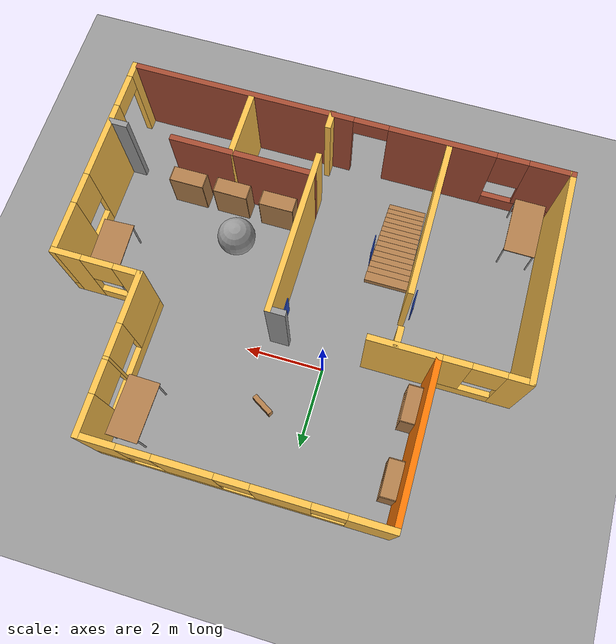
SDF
<sdf version="1.6">
 <world name="default">
  <light name="sun" type="directional">
   <pose>0 0 10 0 -0 0</pose>
   <diffuse>0.8 0.8 0.8 1</diffuse>
   <specular>0.2 0.2 0.2 1</specular>
   <attenuation>
    <range>1000</range>
    <constant>0.9</constant>
    <linear>0.01</linear>
    <quadratic>0.001</quadratic>
   </attenuation>
   <direction>-0.5 0.1 -0.9</direction>
  </light>
  <model name="ground_plane">
   <static>1</static>
   <link name="link">
    <collision name="collision">
     <geometry><plane><normal>0 0 1</normal><size>100 100</size></plane></geometry>
     <surface><friction><ode><mu>100</mu><mu2>50</mu2></ode></friction></surface>
    </collision>
    <visual name="visual">
     <cast_shadows>0</cast_shadows>
     <geometry><plane><normal>0 0 1</normal><size>100 100</size></plane></geometry>
     <material>
      <script><uri>file://media/materials/scripts/gazebo.material</uri><name>Gazebo/Grey</name></script>
     </material>
    </visual>
   </link>
  </model>
  <gravity>0 0 -9.8</gravity>
  <magnetic_field>6e-06 2.3e-05 -4.2e-05</magnetic_field>
  <atmosphere type="adiabatic"/>
  <physics name="default_physics" default="0" type="ode">
   <max_step_size>0.001</max_step_size>
   <real_time_factor>1</real_time_factor>
   <real_time_update_rate>1000</real_time_update_rate>
  </physics>
  <scene><ambient>0.4 0.4 0.4 1</ambient><background>0.7 0.7 0.7 1</background><shadows>1</shadows></scene>
  <spherical_coordinates>
   <surface_model>EARTH_WGS84</surface_model>
   <latitude_deg>0</latitude_deg>
   <longitude_deg>0</longitude_deg>
   <elevation>0</elevation>
   <heading_deg>0</heading_deg>
  </spherical_coordinates>
  <model name="myhome">
   <pose>1.00458 -1.17606 0 0 -0 0</pose>
   <link name="Stairs_0">
    <visual name="Stairs_0_Visual_0">
     <pose>-1.99954 -3.64454 0.083333 0 -0 -3.14159</pose>
     <geometry><box><size>1 0.213511 0.166667</size></box></geometry>
     <material>
      <script><uri>file://media/materials/scripts/gazebo.material</uri><name>Gazebo/Wood</name></script>
      <ambient>0.760784 0.662745 0.627451 1</ambient>
     </material>
     <meta><layer>0</layer></meta>
    </visual>
    <collision name="Stairs_0_Collision_0">
     <geometry><box><size>1 0.213511 0.166667</size></box></geometry>
     <pose>-1.99954 -3.64454 0.083333 0 -0 -3.14159</pose>
    </collision>
    <visual name="Stairs_0_Visual_1">
     <pose>-1.99954 -3.43103 0.25 0 -0 -3.14159</pose>
     <geometry><box><size>1 0.213511 0.166667</size></box></geometry>
     <material>
      <script><uri>file://media/materials/scripts/gazebo.material</uri><name>Gazebo/Wood</name></script>
      <ambient>0.760784 0.662745 0.627451 1</ambient>
     </material>
     <meta><layer>0</layer></meta>
    </visual>
    <collision name="Stairs_0_Collision_1">
     <geometry><box><size>1 0.213511 0.166667</size></box></geometry>
     <pose>-1.99954 -3.43103 0.25 0 -0 -3.14159</pose>
    </collision>
    <visual name="Stairs_0_Visual_2">
     <pose>-1.99954 -3.21752 0.416667 0 -0 -3.14159</pose>
     <geometry><box><size>1 0.213511 0.166667</size></box></geometry>
     <material>
      <script><uri>file://media/materials/scripts/gazebo.material</uri><name>Gazebo/Wood</name></script>
      <ambient>0.760784 0.662745 0.627451 1</ambient>
     </material>
     <meta><layer>0</layer></meta>
    </visual>
    <collision name="Stairs_0_Collision_2">
     <geometry><box><size>1 0.213511 0.166667</size></box></geometry>
     <pose>-1.99954 -3.21752 0.416667 0 -0 -3.14159</pose>
    </collision>
    <visual name="Stairs_0_Visual_3">
     <pose>-1.99954 -3.00401 0.583333 0 -0 -3.14159</pose>
     <geometry><box><size>1 0.213511 0.166667</size></box></geometry>
     <material>
      <script><uri>file://media/materials/scripts/gazebo.material</uri><name>Gazebo/Wood</name></script>
      <ambient>0.760784 0.662745 0.627451 1</ambient>
     </material>
     <meta><layer>0</layer></meta>
    </visual>
    <collision name="Stairs_0_Collision_3">
     <geometry><box><size>1 0.213511 0.166667</size></box></geometry>
     <pose>-1.99954 -3.00401 0.583333 0 -0 -3.14159</pose>
    </collision>
    <visual name="Stairs_0_Visual_4">
     <pose>-1.99954 -2.7905 0.75 0 -0 -3.14159</pose>
     <geometry><box><size>1 0.213511 0.166667</size></box></geometry>
     <material>
      <script><uri>file://media/materials/scripts/gazebo.material</uri><name>Gazebo/Wood</name></script>
      <ambient>0.760784 0.662745 0.627451 1</ambient>
     </material>
     <meta><layer>0</layer></meta>
    </visual>
    <collision name="Stairs_0_Collision_4">
     <geometry><box><size>1 0.213511 0.166667</size></box></geometry>
     <pose>-1.99954 -2.7905 0.75 0 -0 -3.14159</pose>
    </collision>
    <visual name="Stairs_0_Visual_5">
     <pose>-1.99954 -2.57699 0.916667 0 -0 -3.14159</pose>
     <geometry><box><size>1 0.213511 0.166667</size></box></geometry>
     <material>
      <script><uri>file://media/materials/scripts/gazebo.material</uri><name>Gazebo/Wood</name></script>
      <ambient>0.760784 0.662745 0.627451 1</ambient>
     </material>
     <meta><layer>0</layer></meta>
    </visual>
    <collision name="Stairs_0_Collision_5">
     <geometry><box><size>1 0.213511 0.166667</size></box></geometry>
     <pose>-1.99954 -2.57699 0.916667 0 -0 -3.14159</pose>
    </collision>
    <visual name="Stairs_0_Visual_6">
     <pose>-1.99954 -2.36347 1.08333 0 -0 -3.14159</pose>
     <geometry><box><size>1 0.213511 0.166667</size></box></geometry>
     <material>
      <script><uri>file://media/materials/scripts/gazebo.material</uri><name>Gazebo/Wood</name></script>
      <ambient>0.760784 0.662745 0.627451 1</ambient>
     </material>
     <meta><layer>0</layer></meta>
    </visual>
    <collision name="Stairs_0_Collision_6">
     <geometry><box><size>1 0.213511 0.166667</size></box></geometry>
     <pose>-1.99954 -2.36347 1.08333 0 -0 -3.14159</pose>
    </collision>
    <visual name="Stairs_0_Visual_7">
     <pose>-1.99954 -2.14996 1.25 0 -0 -3.14159</pose>
     <geometry><box><size>1 0.213511 0.166667</size></box></geometry>
     <material>
      <script><uri>file://media/materials/scripts/gazebo.material</uri><name>Gazebo/Wood</name></script>
      <ambient>0.760784 0.662745 0.627451 1</ambient>
     </material>
     <meta><layer>0</layer></meta>
    </visual>
    <collision name="Stairs_0_Collision_7">
     <geometry><box><size>1 0.213511 0.166667</size></box></geometry>
     <pose>-1.99954 -2.14996 1.25 0 -0 -3.14159</pose>
    </collision>
    <visual name="Stairs_0_Visual_8">
     <pose>-1.99954 -1.93645 1.41667 0 -0 -3.14159</pose>
     <geometry><box><size>1 0.213511 0.166667</size></box></geometry>
     <material>
      <script><uri>file://media/materials/scripts/gazebo.material</uri><name>Gazebo/Wood</name></script>
      <ambient>0.760784 0.662745 0.627451 1</ambient>
     </material>
     <meta><layer>0</layer></meta>
    </visual>
    <collision name="Stairs_0_Collision_8">
     <geometry><box><size>1 0.213511 0.166667</size></box></geometry>
     <pose>-1.99954 -1.93645 1.41667 0 -0 -3.14159</pose>
    </collision>
    <visual name="Stairs_0_Visual_9">
     <pose>-1.99954 -1.72294 1.58333 0 -0 -3.14159</pose>
     <geometry><box><size>1 0.213511 0.166667</size></box></geometry>
     <material>
      <script><uri>file://media/materials/scripts/gazebo.material</uri><name>Gazebo/Wood</name></script>
      <ambient>0.760784 0.662745 0.627451 1</ambient>
     </material>
     <meta><layer>0</layer></meta>
    </visual>
    <collision name="Stairs_0_Collision_9">
     <geometry><box><size>1 0.213511 0.166667</size></box></geometry>
     <pose>-1.99954 -1.72294 1.58333 0 -0 -3.14159</pose>
    </collision>
    <visual name="Stairs_0_Visual_10">
     <pose>-1.99954 -1.50943 1.75 0 -0 -3.14159</pose>
     <geometry><box><size>1 0.213511 0.166667</size></box></geometry>
     <material>
      <script><uri>file://media/materials/scripts/gazebo.material</uri><name>Gazebo/Wood</name></script>
      <ambient>0.760784 0.662745 0.627451 1</ambient>
     </material>
     <meta><layer>0</layer></meta>
    </visual>
    <collision name="Stairs_0_Collision_10">
     <geometry><box><size>1 0.213511 0.166667</size></box></geometry>
     <pose>-1.99954 -1.50943 1.75 0 -0 -3.14159</pose>
    </collision>
    <visual name="Stairs_0_Visual_11">
     <pose>-1.99954 -1.29592 1.91667 0 -0 -3.14159</pose>
     <geometry><box><size>1 0.213511 0.166667</size></box></geometry>
     <material>
      <script><uri>file://media/materials/scripts/gazebo.material</uri><name>Gazebo/Wood</name></script>
      <ambient>0.760784 0.662745 0.627451 1</ambient>
     </material>
     <meta><layer>0</layer></meta>
    </visual>
    <collision name="Stairs_0_Collision_11">
     <geometry><box><size>1 0.213511 0.166667</size></box></geometry>
     <pose>-1.99954 -1.29592 1.91667 0 -0 -3.14159</pose>
    </collision>
    <visual name="Stairs_0_Visual_12">
     <pose>-1.99954 -1.08241 2.08333 0 -0 -3.14159</pose>
     <geometry><box><size>1 0.213511 0.166667</size></box></geometry>
     <material>
      <script><uri>file://media/materials/scripts/gazebo.material</uri><name>Gazebo/Wood</name></script>
      <ambient>0.760784 0.662745 0.627451 1</ambient>
     </material>
     <meta><layer>0</layer></meta>
    </visual>
    <collision name="Stairs_0_Collision_12">
     <geometry><box><size>1 0.213511 0.166667</size></box></geometry>
     <pose>-1.99954 -1.08241 2.08333 0 -0 -3.14159</pose>
    </collision>
    <visual name="Stairs_0_Visual_13">
     <pose>-1.99954 -0.868895 2.25 0 -0 -3.14159</pose>
     <geometry><box><size>1 0.213511 0.166667</size></box></geometry>
     <material>
      <script><uri>file://media/materials/scripts/gazebo.material</uri><name>Gazebo/Wood</name></script>
      <ambient>0.760784 0.662745 0.627451 1</ambient>
     </material>
     <meta><layer>0</layer></meta>
    </visual>
    <collision name="Stairs_0_Collision_13">
     <geometry><box><size>1 0.213511 0.166667</size></box></geometry>
     <pose>-1.99954 -0.868895 2.25 0 -0 -3.14159</pose>
    </collision>
    <visual name="Stairs_0_Visual_14">
     <pose>-1.99954 -0.655384 2.41667 0 -0 -3.14159</pose>
     <geometry><box><size>1 0.213511 0.166667</size></box></geometry>
     <material>
      <script><uri>file://media/materials/scripts/gazebo.material</uri><name>Gazebo/Wood</name></script>
      <ambient>0.760784 0.662745 0.627451 1</ambient>
     </material>
     <meta><layer>0</layer></meta>
    </visual>
    <collision name="Stairs_0_Collision_14">
     <geometry><box><size>1 0.213511 0.166667</size></box></geometry>
     <pose>-1.99954 -0.655384 2.41667 0 -0 -3.14159</pose>
    </collision>
   </link>
   <link name="Wall_0">
    <pose>0 -4.59248 0 0 -0 3.14159</pose>
    <visual name="Wall_0_Visual_0">
     <pose>-2.79983 0 1.25 0 -0 0</pose>
     <geometry><box><size>5.90034 0.15 2.5</size></box></geometry>
     <material>
      <script><uri>file://media/materials/scripts/gazebo.material</uri><name>Gazebo/Bricks</name></script>
      <ambient>1 0.764706 0.305882 1</ambient>
     </material>
     <meta><layer>0</layer></meta>
    </visual>
    <collision name="Wall_0_Collision_0">
     <geometry><box><size>5.90034 0.15 2.5</size></box></geometry>
     <pose>-2.79983 0 1.25 0 -0 0</pose>
    </collision>
    <visual name="Wall_0_Visual_1">
     <pose>2.41807 0 1.25 0 -0 0</pose>
     <geometry><box><size>2.73546 0.15 2.5</size></box></geometry>
     <material>
      <script><uri>file://media/materials/scripts/gazebo.material</uri><name>Gazebo/Bricks</name></script>
      <ambient>1 0.764706 0.305882 1</ambient>
     </material>
     <meta><layer>0</layer></meta>
    </visual>
    <collision name="Wall_0_Collision_1">
     <geometry><box><size>2.73546 0.15 2.5</size></box></geometry>
     <pose>2.41807 0 1.25 0 -0 0</pose>
    </collision>
    <visual name="Wall_0_Visual_2">
     <pose>4.7679 0 0.25 0 -0 0</pose>
     <geometry><box><size>1.9642 0.15 0.5</size></box></geometry>
     <material>
      <script><uri>file://media/materials/scripts/gazebo.material</uri><name>Gazebo/Bricks</name></script>
      <ambient>1 0.764706 0.305882 1</ambient>
     </material>
     <meta><layer>0</layer></meta>
    </visual>
    <collision name="Wall_0_Collision_2">
     <geometry><box><size>1.9642 0.15 0.5</size></box></geometry>
     <pose>4.7679 0 0.25 0 -0 0</pose>
    </collision>
    <visual name="Wall_0_Visual_3">
     <pose>5.1679 0 1.5 0 -0 0</pose>
     <geometry><box><size>1.1642 0.15 2</size></box></geometry>
     <material>
      <script><uri>file://media/materials/scripts/gazebo.material</uri><name>Gazebo/Bricks</name></script>
      <ambient>1 0.764706 0.305882 1</ambient>
     </material>
     <meta><layer>0</layer></meta>
    </visual>
    <collision name="Wall_0_Collision_3">
     <geometry><box><size>1.1642 0.15 2</size></box></geometry>
     <pose>5.1679 0 1.5 0 -0 0</pose>
    </collision>
    <visual name="Wall_0_Visual_4">
     <pose>4.1858 0 1.9 0 -0 0</pose>
     <geometry><box><size>0.8 0.15 1.2</size></box></geometry>
     <material>
      <script><uri>file://media/materials/scripts/gazebo.material</uri><name>Gazebo/Bricks</name></script>
      <ambient>1 0.764706 0.305882 1</ambient>
     </material>
     <meta><layer>0</layer></meta>
    </visual>
    <collision name="Wall_0_Collision_4">
     <geometry><box><size>0.8 0.15 1.2</size></box></geometry>
     <pose>4.1858 0 1.9 0 -0 0</pose>
    </collision>
    <visual name="Wall_0_Visual_5">
     <pose>0.600338 0 2.25 0 -0 0</pose>
     <geometry><box><size>0.9 0.15 0.5</size></box></geometry>
     <material>
      <script><uri>file://media/materials/scripts/gazebo.material</uri><name>Gazebo/Bricks</name></script>
      <ambient>1 0.764706 0.305882 1</ambient>
     </material>
     <meta><layer>0</layer></meta>
    </visual>
    <collision name="Wall_0_Collision_5">
     <geometry><box><size>0.9 0.15 0.5</size></box></geometry>
     <pose>0.600338 0 2.25 0 -0 0</pose>
    </collision>
   </link>
   <link name="Wall_10">
    <pose>3.525 2.68251 0 0 0 -1.5708</pose>
    <visual name="Wall_10_Visual_0">
     <pose>-1.49909 0 1.25 0 -0 0</pose>
     <geometry><box><size>1.00181 0.15 2.5</size></box></geometry>
     <material>
      <script><uri>file://media/materials/scripts/gazebo.material</uri><name>Gazebo/Grey</name></script>
      <ambient>1 0.764706 0.305882 1</ambient>
     </material>
     <meta><layer>0</layer></meta>
    </visual>
    <collision name="Wall_10_Collision_0">
     <geometry><box><size>1.00181 0.15 2.5</size></box></geometry>
     <pose>-1.49909 0 1.25 0 -0 0</pose>
    </collision>
    <visual name="Wall_10_Visual_1">
     <pose>0.500907 0 0.25 0 -0 0</pose>
     <geometry><box><size>2.99819 0.15 0.5</size></box></geometry>
     <material>
      <script><uri>file://media/materials/scripts/gazebo.material</uri><name>Gazebo/Grey</name></script>
      <ambient>1 0.764706 0.305882 1</ambient>
     </material>
     <meta><layer>0</layer></meta>
    </visual>
    <collision name="Wall_10_Collision_1">
     <geometry><box><size>2.99819 0.15 0.5</size></box></geometry>
     <pose>0.500907 0 0.25 0 -0 0</pose>
    </collision>
    <visual name="Wall_10_Visual_2">
     <pose>-0.160935 0 1.5 0 -0 0</pose>
     <geometry><box><size>0.074503 0.15 2</size></box></geometry>
     <material>
      <script><uri>file://media/materials/scripts/gazebo.material</uri><name>Gazebo/Grey</name></script>
      <ambient>1 0.764706 0.305882 1</ambient>
     </material>
     <meta><layer>0</layer></meta>
    </visual>
    <collision name="Wall_10_Collision_2">
     <geometry><box><size>0.074503 0.15 2</size></box></geometry>
     <pose>-0.160935 0 1.5 0 -0 0</pose>
    </collision>
    <visual name="Wall_10_Visual_3">
     <pose>1.33816 0 1.5 0 -0 0</pose>
     <geometry><box><size>1.32368 0.15 2</size></box></geometry>
     <material>
      <script><uri>file://media/materials/scripts/gazebo.material</uri><name>Gazebo/Grey</name></script>
      <ambient>1 0.764706 0.305882 1</ambient>
     </material>
     <meta><layer>0</layer></meta>
    </visual>
    <collision name="Wall_10_Collision_3">
     <geometry><box><size>1.32368 0.15 2</size></box></geometry>
     <pose>1.33816 0 1.5 0 -0 0</pose>
    </collision>
    <visual name="Wall_10_Visual_4">
     <pose>-0.598187 0 1.9 0 -0 0</pose>
     <geometry><box><size>0.8 0.15 1.2</size></box></geometry>
     <material>
      <script><uri>file://media/materials/scripts/gazebo.material</uri><name>Gazebo/Grey</name></script>
      <ambient>1 0.764706 0.305882 1</ambient>
     </material>
     <meta><layer>0</layer></meta>
    </visual>
    <collision name="Wall_10_Collision_4">
     <geometry><box><size>0.8 0.15 1.2</size></box></geometry>
     <pose>-0.598187 0 1.9 0 -0 0</pose>
    </collision>
    <visual name="Wall_10_Visual_5">
     <pose>0.276316 0 1.9 0 -0 0</pose>
     <geometry><box><size>0.8 0.15 1.2</size></box></geometry>
     <material>
      <script><uri>file://media/materials/scripts/gazebo.material</uri><name>Gazebo/Grey</name></script>
      <ambient>1 0.764706 0.305882 1</ambient>
     </material>
     <meta><layer>0</layer></meta>
    </visual>
    <collision name="Wall_10_Collision_5">
     <geometry><box><size>0.8 0.15 1.2</size></box></geometry>
     <pose>0.276316 0 1.9 0 -0 0</pose>
    </collision>
   </link>
   <link name="Wall_12">
    <collision name="Wall_12_Collision">
     <geometry><box><size>1.75 0.15 2.5</size></box></geometry>
     <pose>0 0 1.25 0 -0 0</pose>
    </collision>
    <visual name="Wall_12_Visual">
     <pose>0 0 1.25 0 -0 0</pose>
     <geometry><box><size>1.75 0.15 2.5</size></box></geometry>
     <material>
      <script><uri>file://media/materials/scripts/gazebo.material</uri><name>Gazebo/Grey</name></script>
      <ambient>1 0.764706 0.305882 1</ambient>
     </material>
     <meta><layer>0</layer></meta>
    </visual>
    <pose>-2.775 0.757515 0 0 -0 0</pose>
   </link>
   <link name="Wall_14">
    <collision name="Wall_14_Collision">
     <geometry><box><size>0.5 0.15 2.5</size></box></geometry>
     <pose>0 0 1.25 0 -0 0</pose>
    </collision>
    <visual name="Wall_14_Visual">
     <pose>0 0 1.25 0 -0 0</pose>
     <geometry><box><size>0.5 0.15 2.5</size></box></geometry>
     <material>
      <script><uri>file://media/materials/scripts/gazebo.material</uri><name>Gazebo/Grey</name></script>
      <ambient>1 0.764706 0.305882 1</ambient>
     </material>
     <meta><layer>0</layer></meta>
    </visual>
    <pose>-2.5942 0.552153 0 0 0 -1.5708</pose>
   </link>
   <link name="Wall_16">
    <collision name="Wall_16_Collision">
     <geometry><box><size>4 0.15 2.5</size></box></geometry>
     <pose>0 0 1.25 0 -0 0</pose>
    </collision>
    <visual name="Wall_16_Visual">
     <pose>0 0 1.25 0 -0 0</pose>
     <geometry><box><size>4 0.15 2.5</size></box></geometry>
     <material>
      <script><uri>file://media/materials/scripts/gazebo.material</uri><name>Gazebo/Grey</name></script>
      <ambient>1 0.764706 0.305882 1</ambient>
     </material>
     <meta><layer>0</layer></meta>
    </visual>
    <pose>-2.6117 -2.5096 0 0 0 -1.5708</pose>
   </link>
   <link name="Wall_18">
    <collision name="Wall_18_Collision">
     <geometry><box><size>0.5 0.15 2.5</size></box></geometry>
     <pose>0 0 1.25 0 -0 0</pose>
    </collision>
    <visual name="Wall_18_Visual">
     <pose>0 0 1.25 0 -0 0</pose>
     <geometry><box><size>0.5 0.15 2.5</size></box></geometry>
     <material>
      <script><uri>file://media/materials/scripts/gazebo.material</uri><name>Gazebo/Grey</name></script>
      <ambient>1 1 1 1</ambient>
     </material>
     <meta><layer>0</layer></meta>
    </visual>
    <pose>0.239285 0.744643 0 0 -0 0</pose>
   </link>
   <link name="Wall_19">
    <collision name="Wall_19_Collision">
     <geometry><box><size>4.25 0.15 2.5</size></box></geometry>
     <pose>0 0 1.25 0 -0 0</pose>
    </collision>
    <visual name="Wall_19_Visual">
     <pose>0 0 1.25 0 -0 0</pose>
     <geometry><box><size>4.25 0.15 2.5</size></box></geometry>
     <material>
      <script><uri>file://media/materials/scripts/gazebo.material</uri><name>Gazebo/Grey</name></script>
      <ambient>1 0.764706 0.305882 1</ambient>
     </material>
     <meta><layer>0</layer></meta>
    </visual>
    <pose>0.414285 -1.30536 0 0 0 -1.5708</pose>
   </link>
   <link name="Wall_2">
    <collision name="Wall_2_Collision">
     <geometry><box><size>5.5 0.15 2.5</size></box></geometry>
     <pose>0 0 1.25 0 -0 0</pose>
    </collision>
    <visual name="Wall_2_Visual">
     <pose>0 0 1.25 0 -0 0</pose>
     <geometry><box><size>5.5 0.15 2.5</size></box></geometry>
     <material>
      <script><uri>file://media/materials/scripts/gazebo.material</uri><name>Gazebo/Grey</name></script>
      <ambient>1 0.764706 0.305882 1</ambient>
     </material>
     <meta><layer>0</layer></meta>
    </visual>
    <pose>-5.675 -1.91749 0 0 -0 1.5708</pose>
   </link>
   <link name="Wall_21">
    <collision name="Wall_21_Collision">
     <geometry><box><size>0.5 0.15 2.5</size></box></geometry>
     <pose>0 0 1.25 0 -0 0</pose>
    </collision>
    <visual name="Wall_21_Visual">
     <pose>0 0 1.25 0 -0 0</pose>
     <geometry><box><size>0.5 0.15 2.5</size></box></geometry>
     <material>
      <script><uri>file://media/materials/scripts/gazebo.material</uri><name>Gazebo/Grey</name></script>
      <ambient>1 0.764706 0.305882 1</ambient>
     </material>
     <meta><layer>0</layer></meta>
    </visual>
    <pose>0.414086 -4.43252 0 0 0 -1.5708</pose>
   </link>
   <link name="Wall_23">
    <collision name="Wall_23_Collision">
     <geometry><box><size>3.75 0.15 2.5</size></box></geometry>
     <pose>0 0 1.25 0 -0 0</pose>
    </collision>
    <visual name="Wall_23_Visual">
     <pose>0 0 1.25 0 -0 0</pose>
     <geometry><box><size>3.75 0.15 2.5</size></box></geometry>
     <material>
      <script><uri>file://media/materials/scripts/gazebo.material</uri><name>Gazebo/Bricks</name></script>
      <ambient>1 0.764706 0.305882 1</ambient>
     </material>
     <meta><layer>0</layer></meta>
    </visual>
    <pose>2.21409 -2.85831 0 0 -0 0</pose>
   </link>
   <link name="Wall_25">
    <collision name="Wall_25_Collision">
     <geometry><box><size>0.5 0.15 2.5</size></box></geometry>
     <pose>0 0 1.25 0 -0 0</pose>
    </collision>
    <visual name="Wall_25_Visual">
     <pose>0 0 1.25 0 -0 0</pose>
     <geometry><box><size>0.5 0.15 2.5</size></box></geometry>
     <material>
      <script><uri>file://media/materials/scripts/gazebo.material</uri><name>Gazebo/Grey</name></script>
      <ambient>1 1 1 1</ambient>
     </material>
     <meta><layer>0</layer></meta>
    </visual>
    <pose>5.46881 -2.8758 0 0 -0 0</pose>
   </link>
   <link name="Wall_27">
    <collision name="Wall_27_Collision">
     <geometry><box><size>1.75 0.15 2.5</size></box></geometry>
     <pose>0 0 1.25 0 -0 0</pose>
    </collision>
    <visual name="Wall_27_Visual">
     <pose>0 0 1.25 0 -0 0</pose>
     <geometry><box><size>1.75 0.15 2.5</size></box></geometry>
     <material>
      <script><uri>file://media/materials/scripts/gazebo.material</uri><name>Gazebo/Grey</name></script>
      <ambient>1 0.764706 0.305882 1</ambient>
     </material>
     <meta><layer>0</layer></meta>
    </visual>
    <pose>2.51289 -3.65831 0 0 0 -1.5708</pose>
   </link>
   <link name="Wall_3">
    <pose>-4.625 0.757515 0 0 -0 0</pose>
    <visual name="Wall_3_Visual_0">
     <pose>-0.813996 0 1.25 0 -0 0</pose>
     <geometry><box><size>0.622008 0.15 2.5</size></box></geometry>
     <material>
      <script><uri>file://media/materials/scripts/gazebo.material</uri><name>Gazebo/Grey</name></script>
      <ambient>1 0.764706 0.305882 1</ambient>
     </material>
     <meta><layer>0</layer></meta>
    </visual>
    <collision name="Wall_3_Collision_0">
     <geometry><box><size>0.622008 0.15 2.5</size></box></geometry>
     <pose>-0.813996 0 1.25 0 -0 0</pose>
    </collision>
    <visual name="Wall_3_Visual_1">
     <pose>0.311004 0 0.25 0 -0 0</pose>
     <geometry><box><size>1.62799 0.15 0.5</size></box></geometry>
     <material>
      <script><uri>file://media/materials/scripts/gazebo.material</uri><name>Gazebo/Grey</name></script>
      <ambient>1 0.764706 0.305882 1</ambient>
     </material>
     <meta><layer>0</layer></meta>
    </visual>
    <collision name="Wall_3_Collision_1">
     <geometry><box><size>1.62799 0.15 0.5</size></box></geometry>
     <pose>0.311004 0 0.25 0 -0 0</pose>
    </collision>
    <visual name="Wall_3_Visual_2">
     <pose>0.711004 0 1.5 0 -0 0</pose>
     <geometry><box><size>0.827992 0.15 2</size></box></geometry>
     <material>
      <script><uri>file://media/materials/scripts/gazebo.material</uri><name>Gazebo/Grey</name></script>
      <ambient>1 0.764706 0.305882 1</ambient>
     </material>
     <meta><layer>0</layer></meta>
    </visual>
    <collision name="Wall_3_Collision_2">
     <geometry><box><size>0.827992 0.15 2</size></box></geometry>
     <pose>0.711004 0 1.5 0 -0 0</pose>
    </collision>
    <visual name="Wall_3_Visual_3">
     <pose>-0.102992 0 1.9 0 -0 0</pose>
     <geometry><box><size>0.8 0.15 1.2</size></box></geometry>
     <material>
      <script><uri>file://media/materials/scripts/gazebo.material</uri><name>Gazebo/Grey</name></script>
      <ambient>1 0.764706 0.305882 1</ambient>
     </material>
     <meta><layer>0</layer></meta>
    </visual>
    <collision name="Wall_3_Collision_3">
     <geometry><box><size>0.8 0.15 1.2</size></box></geometry>
     <pose>-0.102992 0 1.9 0 -0 0</pose>
    </collision>
   </link>
   <link name="Wall_5">
    <pose>5.675 -1.91749 0 0 -0 1.5708</pose>
    <visual name="Wall_5_Visual_0">
     <pose>-2.5339 0 1.25 0 -0 0</pose>
     <geometry><box><size>0.432201 0.15 2.5</size></box></geometry>
     <material>
      <script><uri>file://media/materials/scripts/gazebo.material</uri><name>Gazebo/Grey</name></script>
      <ambient>1 0.764706 0.305882 1</ambient>
     </material>
     <meta><layer>0</layer></meta>
    </visual>
    <collision name="Wall_5_Collision_0">
     <geometry><box><size>0.432201 0.15 2.5</size></box></geometry>
     <pose>-2.5339 0 1.25 0 -0 0</pose>
    </collision>
    <visual name="Wall_5_Visual_1">
     <pose>-0.408613 0 1.25 0 -0 0</pose>
     <geometry><box><size>2.01837 0.15 2.5</size></box></geometry>
     <material>
      <script><uri>file://media/materials/scripts/gazebo.material</uri><name>Gazebo/Grey</name></script>
      <ambient>1 0.764706 0.305882 1</ambient>
     </material>
     <meta><layer>0</layer></meta>
    </visual>
    <collision name="Wall_5_Collision_1">
     <geometry><box><size>2.01837 0.15 2.5</size></box></geometry>
     <pose>-0.408613 0 1.25 0 -0 0</pose>
    </collision>
    <visual name="Wall_5_Visual_2">
     <pose>1.67529 0 0.25 0 -0 0</pose>
     <geometry><box><size>2.14943 0.15 0.5</size></box></geometry>
     <material>
      <script><uri>file://media/materials/scripts/gazebo.material</uri><name>Gazebo/Grey</name></script>
      <ambient>1 0.764706 0.305882 1</ambient>
     </material>
     <meta><layer>0</layer></meta>
    </visual>
    <collision name="Wall_5_Collision_2">
     <geometry><box><size>2.14943 0.15 0.5</size></box></geometry>
     <pose>1.67529 0 0.25 0 -0 0</pose>
    </collision>
    <visual name="Wall_5_Visual_3">
     <pose>2.07529 0 1.5 0 -0 0</pose>
     <geometry><box><size>1.34943 0.15 2</size></box></geometry>
     <material>
      <script><uri>file://media/materials/scripts/gazebo.material</uri><name>Gazebo/Grey</name></script>
      <ambient>1 0.764706 0.305882 1</ambient>
     </material>
     <meta><layer>0</layer></meta>
    </visual>
    <collision name="Wall_5_Collision_3">
     <geometry><box><size>1.34943 0.15 2</size></box></geometry>
     <pose>2.07529 0 1.5 0 -0 0</pose>
    </collision>
    <visual name="Wall_5_Visual_4">
     <pose>1.00057 0 1.9 0 -0 0</pose>
     <geometry><box><size>0.8 0.15 1.2</size></box></geometry>
     <material>
      <script><uri>file://media/materials/scripts/gazebo.material</uri><name>Gazebo/Grey</name></script>
      <ambient>1 0.764706 0.305882 1</ambient>
     </material>
     <meta><layer>0</layer></meta>
    </visual>
    <collision name="Wall_5_Collision_4">
     <geometry><box><size>0.8 0.15 1.2</size></box></geometry>
     <pose>1.00057 0 1.9 0 -0 0</pose>
    </collision>
    <visual name="Wall_5_Visual_5">
     <pose>-1.8678 0 2.25 0 -0 0</pose>
     <geometry><box><size>0.9 0.15 0.5</size></box></geometry>
     <material>
      <script><uri>file://media/materials/scripts/gazebo.material</uri><name>Gazebo/Grey</name></script>
      <ambient>1 0.764706 0.305882 1</ambient>
     </material>
     <meta><layer>0</layer></meta>
    </visual>
    <collision name="Wall_5_Collision_5">
     <geometry><box><size>0.9 0.15 0.5</size></box></geometry>
     <pose>-1.8678 0 2.25 0 -0 0</pose>
    </collision>
   </link>
   <link name="Wall_6">
    <pose>4.625 0.757515 0 0 -0 3.14159</pose>
    <visual name="Wall_6_Visual_0">
     <pose>-0.73836 0 1.25 0 -0 0</pose>
     <geometry><box><size>0.773279 0.15 2.5</size></box></geometry>
     <material>
      <script><uri>file://media/materials/scripts/gazebo.material</uri><name>Gazebo/Grey</name></script>
      <ambient>1 0.764706 0.305882 1</ambient>
     </material>
     <meta><layer>0</layer></meta>
    </visual>
    <collision name="Wall_6_Collision_0">
     <geometry><box><size>0.773279 0.15 2.5</size></box></geometry>
     <pose>-0.73836 0 1.25 0 -0 0</pose>
    </collision>
    <visual name="Wall_6_Visual_1">
     <pose>0.38664 0 0.25 0 -0 0</pose>
     <geometry><box><size>1.47672 0.15 0.5</size></box></geometry>
     <material>
      <script><uri>file://media/materials/scripts/gazebo.material</uri><name>Gazebo/Grey</name></script>
      <ambient>1 0.764706 0.305882 1</ambient>
     </material>
     <meta><layer>0</layer></meta>
    </visual>
    <collision name="Wall_6_Collision_1">
     <geometry><box><size>1.47672 0.15 0.5</size></box></geometry>
     <pose>0.38664 0 0.25 0 -0 0</pose>
    </collision>
    <visual name="Wall_6_Visual_2">
     <pose>0.78664 0 1.5 0 -0 0</pose>
     <geometry><box><size>0.676721 0.15 2</size></box></geometry>
     <material>
      <script><uri>file://media/materials/scripts/gazebo.material</uri><name>Gazebo/Grey</name></script>
      <ambient>1 0.764706 0.305882 1</ambient>
     </material>
     <meta><layer>0</layer></meta>
    </visual>
    <collision name="Wall_6_Collision_2">
     <geometry><box><size>0.676721 0.15 2</size></box></geometry>
     <pose>0.78664 0 1.5 0 -0 0</pose>
    </collision>
    <visual name="Wall_6_Visual_3">
     <pose>0.048279 0 1.9 0 -0 0</pose>
     <geometry><box><size>0.8 0.15 1.2</size></box></geometry>
     <material>
      <script><uri>file://media/materials/scripts/gazebo.material</uri><name>Gazebo/Grey</name></script>
      <ambient>1 0.764706 0.305882 1</ambient>
     </material>
     <meta><layer>0</layer></meta>
    </visual>
    <collision name="Wall_6_Collision_3">
     <geometry><box><size>0.8 0.15 1.2</size></box></geometry>
     <pose>0.048279 0 1.9 0 -0 0</pose>
    </collision>
   </link>
   <link name="Wall_8">
    <collision name="Wall_8_Collision">
     <geometry><box><size>4 0.15 2.5</size></box></geometry>
     <pose>0 0 1.25 0 -0 0</pose>
    </collision>
    <visual name="Wall_8_Visual">
     <pose>0 0 1.25 0 -0 0</pose>
     <geometry><box><size>4 0.15 2.5</size></box></geometry>
     <material>
      <script><uri>file://media/materials/scripts/gazebo.material</uri><name>Gazebo/Grey</name></script>
      <ambient>0.996078 0.47451 0.0196078 1</ambient>
     </material>
     <meta><layer>0</layer></meta>
    </visual>
    <pose>-3.575 2.68251 0 0 -0 1.5708</pose>
   </link>
   <link name="Wall_9">
    <pose>-0.025 4.60752 0 0 -0 0</pose>
    <visual name="Wall_9_Visual_0">
     <pose>-3.06973 0 1.25 0 -0 0</pose>
     <geometry><box><size>1.11054 0.15 2.5</size></box></geometry>
     <material>
      <script><uri>file://media/materials/scripts/gazebo.material</uri><name>Gazebo/Grey</name></script>
      <ambient>1 0.764706 0.305882 1</ambient>
     </material>
     <meta><layer>0</layer></meta>
    </visual>
    <collision name="Wall_9_Collision_0">
     <geometry><box><size>1.11054 0.15 2.5</size></box></geometry>
     <pose>-3.06973 0 1.25 0 -0 0</pose>
    </collision>
    <visual name="Wall_9_Visual_1">
     <pose>0.555269 0 0.25 0 -0 0</pose>
     <geometry><box><size>6.13946 0.15 0.5</size></box></geometry>
     <material>
      <script><uri>file://media/materials/scripts/gazebo.material</uri><name>Gazebo/Grey</name></script>
      <ambient>1 0.764706 0.305882 1</ambient>
     </material>
     <meta><layer>0</layer></meta>
    </visual>
    <collision name="Wall_9_Collision_1">
     <geometry><box><size>6.13946 0.15 0.5</size></box></geometry>
     <pose>0.555269 0 0.25 0 -0 0</pose>
    </collision>
    <visual name="Wall_9_Visual_2">
     <pose>-1.03882 0 1.5 0 -0 0</pose>
     <geometry><box><size>1.35128 0.15 2</size></box></geometry>
     <material>
      <script><uri>file://media/materials/scripts/gazebo.material</uri><name>Gazebo/Grey</name></script>
      <ambient>1 0.764706 0.305882 1</ambient>
     </material>
     <meta><layer>0</layer></meta>
    </visual>
    <collision name="Wall_9_Collision_2">
     <geometry><box><size>1.35128 0.15 2</size></box></geometry>
     <pose>-1.03882 0 1.5 0 -0 0</pose>
    </collision>
    <visual name="Wall_9_Visual_3">
     <pose>1.13869 0 1.5 0 -0 0</pose>
     <geometry><box><size>1.40375 0.15 2</size></box></geometry>
     <material>
      <script><uri>file://media/materials/scripts/gazebo.material</uri><name>Gazebo/Grey</name></script>
      <ambient>1 0.764706 0.305882 1</ambient>
     </material>
     <meta><layer>0</layer></meta>
    </visual>
    <collision name="Wall_9_Collision_3">
     <geometry><box><size>1.40375 0.15 2</size></box></geometry>
     <pose>1.13869 0 1.5 0 -0 0</pose>
    </collision>
    <visual name="Wall_9_Visual_4">
     <pose>3.13278 0 1.5 0 -0 0</pose>
     <geometry><box><size>0.984438 0.15 2</size></box></geometry>
     <material>
      <script><uri>file://media/materials/scripts/gazebo.material</uri><name>Gazebo/Grey</name></script>
      <ambient>1 0.764706 0.305882 1</ambient>
     </material>
     <meta><layer>0</layer></meta>
    </visual>
    <collision name="Wall_9_Collision_4">
     <geometry><box><size>0.984438 0.15 2</size></box></geometry>
     <pose>3.13278 0 1.5 0 -0 0</pose>
    </collision>
    <visual name="Wall_9_Visual_5">
     <pose>-2.11446 0 1.9 0 -0 0</pose>
     <geometry><box><size>0.8 0.15 1.2</size></box></geometry>
     <material>
      <script><uri>file://media/materials/scripts/gazebo.material</uri><name>Gazebo/Grey</name></script>
      <ambient>1 0.764706 0.305882 1</ambient>
     </material>
     <meta><layer>0</layer></meta>
    </visual>
    <collision name="Wall_9_Collision_5">
     <geometry><box><size>0.8 0.15 1.2</size></box></geometry>
     <pose>-2.11446 0 1.9 0 -0 0</pose>
    </collision>
    <visual name="Wall_9_Visual_6">
     <pose>0.036815 0 1.9 0 -0 0</pose>
     <geometry><box><size>0.8 0.15 1.2</size></box></geometry>
     <material>
      <script><uri>file://media/materials/scripts/gazebo.material</uri><name>Gazebo/Grey</name></script>
      <ambient>1 0.764706 0.305882 1</ambient>
     </material>
     <meta><layer>0</layer></meta>
    </visual>
    <collision name="Wall_9_Collision_6">
     <geometry><box><size>0.8 0.15 1.2</size></box></geometry>
     <pose>0.036815 0 1.9 0 -0 0</pose>
    </collision>
    <visual name="Wall_9_Visual_7">
     <pose>2.24056 0 1.9 0 -0 0</pose>
     <geometry><box><size>0.8 0.15 1.2</size></box></geometry>
     <material>
      <script><uri>file://media/materials/scripts/gazebo.material</uri><name>Gazebo/Grey</name></script>
      <ambient>1 0.764706 0.305882 1</ambient>
     </material>
     <meta><layer>0</layer></meta>
    </visual>
    <collision name="Wall_9_Collision_7">
     <geometry><box><size>0.8 0.15 1.2</size></box></geometry>
     <pose>2.24056 0 1.9 0 -0 0</pose>
    </collision>
   </link>
   <static>1</static>
  </model>
  <model name="bookshelf">
   <static>1</static>
   <link name="link">
    <inertial><mass>1</mass></inertial>
    <collision name="back">
     <pose>0 0.005 0.6 0 -0 0</pose>
     <geometry><box><size>0.9 0.01 1.2</size></box></geometry>
    </collision>
    <visual name="visual1">
     <pose>0 0.005 0.6 0 -0 0</pose>
     <geometry><box><size>0.9 0.01 1.2</size></box></geometry>
     <material>
      <script><uri>file://media/materials/scripts/gazebo.material</uri><name>Gazebo/Wood</name></script>
     </material>
    </visual>
    <collision name="left_side">
     <pose>0.45 -0.195 0.6 0 -0 0</pose>
     <geometry><box><size>0.02 0.4 1.2</size></box></geometry>
    </collision>
    <visual name="visual2">
     <pose>0.45 -0.195 0.6 0 -0 0</pose>
     <geometry><box><size>0.02 0.4 1.2</size></box></geometry>
     <material>
      <script><uri>file://media/materials/scripts/gazebo.material</uri><name>Gazebo/Wood</name></script>
     </material>
    </visual>
    <collision name="right_side">
     <pose>-0.45 -0.195 0.6 0 -0 0</pose>
     <geometry><box><size>0.02 0.4 1.2</size></box></geometry>
    </collision>
    <visual name="visual3">
     <pose>-0.45 -0.195 0.6 0 -0 0</pose>
     <geometry><box><size>0.02 0.4 1.2</size></box></geometry>
     <material>
      <script><uri>file://media/materials/scripts/gazebo.material</uri><name>Gazebo/Wood</name></script>
     </material>
    </visual>
    <collision name="bottom">
     <pose>0 -0.195 0.03 0 -0 0</pose>
     <geometry><box><size>0.88 0.4 0.06</size></box></geometry>
    </collision>
    <visual name="visual4">
     <pose>0 -0.195 0.03 0 -0 0</pose>
     <geometry><box><size>0.88 0.4 0.06</size></box></geometry>
     <material>
      <script><uri>file://media/materials/scripts/gazebo.material</uri><name>Gazebo/Wood</name></script>
     </material>
    </visual>
    <collision name="top">
     <pose>0 -0.195 1.19 0 -0 0</pose>
     <geometry><box><size>0.88 0.4 0.02</size></box></geometry>
    </collision>
    <visual name="visual5">
     <pose>0 -0.195 1.19 0 -0 0</pose>
     <geometry><box><size>0.88 0.4 0.02</size></box></geometry>
     <material>
      <script><uri>file://media/materials/scripts/gazebo.material</uri><name>Gazebo/Wood</name></script>
     </material>
    </visual>
    <collision name="low_shelf">
     <pose>0 -0.195 0.43 0 -0 0</pose>
     <geometry><box><size>0.88 0.4 0.02</size></box></geometry>
    </collision>
    <visual name="visual6">
     <pose>0 -0.195 0.43 0 -0 0</pose>
     <geometry><box><size>0.88 0.4 0.02</size></box></geometry>
     <material>
      <script><uri>file://media/materials/scripts/gazebo.material</uri><name>Gazebo/Wood</name></script>
     </material>
    </visual>
    <collision name="high_shelf">
     <pose>0 -0.195 0.8 0 -0 0</pose>
     <geometry><box><size>0.88 0.4 0.02</size></box></geometry>
    </collision>
    <visual name="visual7">
     <pose>0 -0.195 0.8 0 -0 0</pose>
     <geometry><box><size>0.88 0.4 0.02</size></box></geometry>
     <material>
      <script><uri>file://media/materials/scripts/gazebo.material</uri><name>Gazebo/Wood</name></script>
     </material>
    </visual>
   </link>
   <pose>-2.52423 2.27115 0 0.010486 0.000465 1.57369</pose>
  </model>
  <model name="bookshelf_0">
   <static>1</static>
   <link name="link">
    <inertial><mass>1</mass></inertial>
    <collision name="back">
     <pose>0 0.005 0.6 0 -0 0</pose>
     <geometry><box><size>0.9 0.01 1.2</size></box></geometry>
    </collision>
    <visual name="visual1">
     <pose>0 0.005 0.6 0 -0 0</pose>
     <geometry><box><size>0.9 0.01 1.2</size></box></geometry>
     <material>
      <script><uri>file://media/materials/scripts/gazebo.material</uri><name>Gazebo/Wood</name></script>
     </material>
    </visual>
    <collision name="left_side">
     <pose>0.45 -0.195 0.6 0 -0 0</pose>
     <geometry><box><size>0.02 0.4 1.2</size></box></geometry>
    </collision>
    <visual name="visual2">
     <pose>0.45 -0.195 0.6 0 -0 0</pose>
     <geometry><box><size>0.02 0.4 1.2</size></box></geometry>
     <material>
      <script><uri>file://media/materials/scripts/gazebo.material</uri><name>Gazebo/Wood</name></script>
     </material>
    </visual>
    <collision name="right_side">
     <pose>-0.45 -0.195 0.6 0 -0 0</pose>
     <geometry><box><size>0.02 0.4 1.2</size></box></geometry>
    </collision>
    <visual name="visual3">
     <pose>-0.45 -0.195 0.6 0 -0 0</pose>
     <geometry><box><size>0.02 0.4 1.2</size></box></geometry>
     <material>
      <script><uri>file://media/materials/scripts/gazebo.material</uri><name>Gazebo/Wood</name></script>
     </material>
    </visual>
    <collision name="bottom">
     <pose>0 -0.195 0.03 0 -0 0</pose>
     <geometry><box><size>0.88 0.4 0.06</size></box></geometry>
    </collision>
    <visual name="visual4">
     <pose>0 -0.195 0.03 0 -0 0</pose>
     <geometry><box><size>0.88 0.4 0.06</size></box></geometry>
     <material>
      <script><uri>file://media/materials/scripts/gazebo.material</uri><name>Gazebo/Wood</name></script>
     </material>
    </visual>
    <collision name="top">
     <pose>0 -0.195 1.19 0 -0 0</pose>
     <geometry><box><size>0.88 0.4 0.02</size></box></geometry>
    </collision>
    <visual name="visual5">
     <pose>0 -0.195 1.19 0 -0 0</pose>
     <geometry><box><size>0.88 0.4 0.02</size></box></geometry>
     <material>
      <script><uri>file://media/materials/scripts/gazebo.material</uri><name>Gazebo/Wood</name></script>
     </material>
    </visual>
    <collision name="low_shelf">
     <pose>0 -0.195 0.43 0 -0 0</pose>
     <geometry><box><size>0.88 0.4 0.02</size></box></geometry>
    </collision>
    <visual name="visual6">
     <pose>0 -0.195 0.43 0 -0 0</pose>
     <geometry><box><size>0.88 0.4 0.02</size></box></geometry>
     <material>
      <script><uri>file://media/materials/scripts/gazebo.material</uri><name>Gazebo/Wood</name></script>
     </material>
    </visual>
    <collision name="high_shelf">
     <pose>0 -0.195 0.8 0 -0 0</pose>
     <geometry><box><size>0.88 0.4 0.02</size></box></geometry>
    </collision>
    <visual name="visual7">
     <pose>0 -0.195 0.8 0 -0 0</pose>
     <geometry><box><size>0.88 0.4 0.02</size></box></geometry>
     <material>
      <script><uri>file://media/materials/scripts/gazebo.material</uri><name>Gazebo/Wood</name></script>
     </material>
    </visual>
   </link>
   <pose>-2.53606 0.48798 0 0 -0 1.57894</pose>
  </model>
  <model name="table">
   <static>1</static>
   <link name="link">
    <collision name="surface">
     <pose>0 0 1 0 -0 0</pose>
     <geometry><box><size>1.5 0.8 0.03</size></box></geometry>
     <surface><friction><ode><mu>0.6</mu><mu2>0.6</mu2></ode></friction></surface>
    </collision>
    <visual name="visual1">
     <pose>0 0 1 0 -0 0</pose>
     <geometry><box><size>1.5 0.8 0.03</size></box></geometry>
     <material>
      <script><uri>file://media/materials/scripts/gazebo.material</uri><name>Gazebo/Wood</name></script>
     </material>
    </visual>
    <collision name="front_left_leg">
     <pose>0.68 0.38 0.5 0 -0 0</pose>
     <geometry><cylinder><radius>0.02</radius><length>1</length></cylinder></geometry>
    </collision>
    <visual name="front_left_leg">
     <pose>0.68 0.38 0.5 0 -0 0</pose>
     <geometry><cylinder><radius>0.02</radius><length>1</length></cylinder></geometry>
     <material>
      <script><uri>file://media/materials/scripts/gazebo.material</uri><name>Gazebo/Grey</name></script>
     </material>
    </visual>
    <collision name="front_right_leg">
     <pose>0.68 -0.38 0.5 0 -0 0</pose>
     <geometry><cylinder><radius>0.02</radius><length>1</length></cylinder></geometry>
    </collision>
    <visual name="front_right_leg">
     <pose>0.68 -0.38 0.5 0 -0 0</pose>
     <geometry><cylinder><radius>0.02</radius><length>1</length></cylinder></geometry>
     <material>
      <script><uri>file://media/materials/scripts/gazebo.material</uri><name>Gazebo/Grey</name></script>
     </material>
    </visual>
    <collision name="back_right_leg">
     <pose>-0.68 -0.38 0.5 0 -0 0</pose>
     <geometry><cylinder><radius>0.02</radius><length>1</length></cylinder></geometry>
    </collision>
    <visual name="back_right_leg">
     <pose>-0.68 -0.38 0.5 0 -0 0</pose>
     <geometry><cylinder><radius>0.02</radius><length>1</length></cylinder></geometry>
     <material>
      <script><uri>file://media/materials/scripts/gazebo.material</uri><name>Gazebo/Grey</name></script>
     </material>
    </visual>
    <collision name="back_left_leg">
     <pose>-0.68 0.38 0.5 0 -0 0</pose>
     <geometry><cylinder><radius>0.02</radius><length>1</length></cylinder></geometry>
    </collision>
    <visual name="back_left_leg">
     <pose>-0.68 0.38 0.5 0 -0 0</pose>
     <geometry><cylinder><radius>0.02</radius><length>1</length></cylinder></geometry>
     <material>
      <script><uri>file://media/materials/scripts/gazebo.material</uri><name>Gazebo/Grey</name></script>
     </material>
    </visual>
   </link>
   <pose>3.97398 2.37676 0 0 -0 1.55172</pose>
  </model>
  <model name="ground_plane_0">
   <static>1</static>
   <link name="link">
    <collision name="collision">
     <geometry><plane><normal>0 0 1</normal><size>100 100</size></plane></geometry>
     <surface><friction><ode><mu>100</mu><mu2>50</mu2></ode></friction></surface>
    </collision>
    <visual name="visual">
     <cast_shadows>0</cast_shadows>
     <geometry><plane><normal>0 0 1</normal><size>100 100</size></plane></geometry>
     <material>
      <script><uri>file://media/materials/scripts/gazebo.material</uri><name>Gazebo/Grey</name></script>
     </material>
    </visual>
   </link>
   <pose>2.55488 -2.2574 0 0 -0 0</pose>
  </model>
  <model name="table_0">
   <static>1</static>
   <link name="link">
    <collision name="surface">
     <pose>0 0 1 0 -0 0</pose>
     <geometry><box><size>1.5 0.8 0.03</size></box></geometry>
     <surface><friction><ode><mu>0.6</mu><mu2>0.6</mu2></ode></friction></surface>
    </collision>
    <visual name="visual1">
     <pose>0 0 1 0 -0 0</pose>
     <geometry><box><size>1.5 0.8 0.03</size></box></geometry>
     <material>
      <script><uri>file://media/materials/scripts/gazebo.material</uri><name>Gazebo/Wood</name></script>
     </material>
    </visual>
    <collision name="front_left_leg">
     <pose>0.68 0.38 0.5 0 -0 0</pose>
     <geometry><cylinder><radius>0.02</radius><length>1</length></cylinder></geometry>
    </collision>
    <visual name="front_left_leg">
     <pose>0.68 0.38 0.5 0 -0 0</pose>
     <geometry><cylinder><radius>0.02</radius><length>1</length></cylinder></geometry>
     <material>
      <script><uri>file://media/materials/scripts/gazebo.material</uri><name>Gazebo/Grey</name></script>
     </material>
    </visual>
    <collision name="front_right_leg">
     <pose>0.68 -0.38 0.5 0 -0 0</pose>
     <geometry><cylinder><radius>0.02</radius><length>1</length></cylinder></geometry>
    </collision>
    <visual name="front_right_leg">
     <pose>0.68 -0.38 0.5 0 -0 0</pose>
     <geometry><cylinder><radius>0.02</radius><length>1</length></cylinder></geometry>
     <material>
      <script><uri>file://media/materials/scripts/gazebo.material</uri><name>Gazebo/Grey</name></script>
     </material>
    </visual>
    <collision name="back_right_leg">
     <pose>-0.68 -0.38 0.5 0 -0 0</pose>
     <geometry><cylinder><radius>0.02</radius><length>1</length></cylinder></geometry>
    </collision>
    <visual name="back_right_leg">
     <pose>-0.68 -0.38 0.5 0 -0 0</pose>
     <geometry><cylinder><radius>0.02</radius><length>1</length></cylinder></geometry>
     <material>
      <script><uri>file://media/materials/scripts/gazebo.material</uri><name>Gazebo/Grey</name></script>
     </material>
    </visual>
    <collision name="back_left_leg">
     <pose>-0.68 0.38 0.5 0 -0 0</pose>
     <geometry><cylinder><radius>0.02</radius><length>1</length></cylinder></geometry>
    </collision>
    <visual name="back_left_leg">
     <pose>-0.68 0.38 0.5 0 -0 0</pose>
     <geometry><cylinder><radius>0.02</radius><length>1</length></cylinder></geometry>
     <material>
      <script><uri>file://media/materials/scripts/gazebo.material</uri><name>Gazebo/Grey</name></script>
     </material>
    </visual>
   </link>
   <pose>-4.03117 -4.81166 0 0 0 -1.57951</pose>
  </model>
  <model name="table_1">
   <static>1</static>
   <link name="link">
    <collision name="surface">
     <pose>0 0 1 0 -0 0</pose>
     <geometry><box><size>1.5 0.8 0.03</size></box></geometry>
     <surface><friction><ode><mu>0.6</mu><mu2>0.6</mu2></ode></friction></surface>
    </collision>
    <visual name="visual1">
     <pose>0 0 1 0 -0 0</pose>
     <geometry><box><size>1.5 0.8 0.03</size></box></geometry>
     <material>
      <script><uri>file://media/materials/scripts/gazebo.material</uri><name>Gazebo/Wood</name></script>
     </material>
    </visual>
    <collision name="front_left_leg">
     <pose>0.68 0.38 0.5 0 -0 0</pose>
     <geometry><cylinder><radius>0.02</radius><length>1</length></cylinder></geometry>
    </collision>
    <visual name="front_left_leg">
     <pose>0.68 0.38 0.5 0 -0 0</pose>
     <geometry><cylinder><radius>0.02</radius><length>1</length></cylinder></geometry>
     <material>
      <script><uri>file://media/materials/scripts/gazebo.material</uri><name>Gazebo/Grey</name></script>
     </material>
    </visual>
    <collision name="front_right_leg">
     <pose>0.68 -0.38 0.5 0 -0 0</pose>
     <geometry><cylinder><radius>0.02</radius><length>1</length></cylinder></geometry>
    </collision>
    <visual name="front_right_leg">
     <pose>0.68 -0.38 0.5 0 -0 0</pose>
     <geometry><cylinder><radius>0.02</radius><length>1</length></cylinder></geometry>
     <material>
      <script><uri>file://media/materials/scripts/gazebo.material</uri><name>Gazebo/Grey</name></script>
     </material>
    </visual>
    <collision name="back_right_leg">
     <pose>-0.68 -0.38 0.5 0 -0 0</pose>
     <geometry><cylinder><radius>0.02</radius><length>1</length></cylinder></geometry>
    </collision>
    <visual name="back_right_leg">
     <pose>-0.68 -0.38 0.5 0 -0 0</pose>
     <geometry><cylinder><radius>0.02</radius><length>1</length></cylinder></geometry>
     <material>
      <script><uri>file://media/materials/scripts/gazebo.material</uri><name>Gazebo/Grey</name></script>
     </material>
    </visual>
    <collision name="back_left_leg">
     <pose>-0.68 0.38 0.5 0 -0 0</pose>
     <geometry><cylinder><radius>0.02</radius><length>1</length></cylinder></geometry>
    </collision>
    <visual name="back_left_leg">
     <pose>-0.68 0.38 0.5 0 -0 0</pose>
     <geometry><cylinder><radius>0.02</radius><length>1</length></cylinder></geometry>
     <material>
      <script><uri>file://media/materials/scripts/gazebo.material</uri><name>Gazebo/Grey</name></script>
     </material>
    </visual>
   </link>
   <pose>6.01108 -1.30901 0 0 0 -1.52855</pose>
  </model>
  <model name="bookshelf_1">
   <static>1</static>
   <link name="link">
    <inertial><mass>1</mass></inertial>
    <collision name="back">
     <pose>0 0.005 0.6 0 -0 0</pose>
     <geometry><box><size>0.9 0.01 1.2</size></box></geometry>
    </collision>
    <visual name="visual1">
     <pose>0 0.005 0.6 0 -0 0</pose>
     <geometry><box><size>0.9 0.01 1.2</size></box></geometry>
     <material>
      <script><uri>file://media/materials/scripts/gazebo.material</uri><name>Gazebo/Wood</name></script>
     </material>
    </visual>
    <collision name="left_side">
     <pose>0.45 -0.195 0.6 0 -0 0</pose>
     <geometry><box><size>0.02 0.4 1.2</size></box></geometry>
    </collision>
    <visual name="visual2">
     <pose>0.45 -0.195 0.6 0 -0 0</pose>
     <geometry><box><size>0.02 0.4 1.2</size></box></geometry>
     <material>
      <script><uri>file://media/materials/scripts/gazebo.material</uri><name>Gazebo/Wood</name></script>
     </material>
    </visual>
    <collision name="right_side">
     <pose>-0.45 -0.195 0.6 0 -0 0</pose>
     <geometry><box><size>0.02 0.4 1.2</size></box></geometry>
    </collision>
    <visual name="visual3">
     <pose>-0.45 -0.195 0.6 0 -0 0</pose>
     <geometry><box><size>0.02 0.4 1.2</size></box></geometry>
     <material>
      <script><uri>file://media/materials/scripts/gazebo.material</uri><name>Gazebo/Wood</name></script>
     </material>
    </visual>
    <collision name="bottom">
     <pose>0 -0.195 0.03 0 -0 0</pose>
     <geometry><box><size>0.88 0.4 0.06</size></box></geometry>
    </collision>
    <visual name="visual4">
     <pose>0 -0.195 0.03 0 -0 0</pose>
     <geometry><box><size>0.88 0.4 0.06</size></box></geometry>
     <material>
      <script><uri>file://media/materials/scripts/gazebo.material</uri><name>Gazebo/Wood</name></script>
     </material>
    </visual>
    <collision name="top">
     <pose>0 -0.195 1.19 0 -0 0</pose>
     <geometry><box><size>0.88 0.4 0.02</size></box></geometry>
    </collision>
    <visual name="visual5">
     <pose>0 -0.195 1.19 0 -0 0</pose>
     <geometry><box><size>0.88 0.4 0.02</size></box></geometry>
     <material>
      <script><uri>file://media/materials/scripts/gazebo.material</uri><name>Gazebo/Wood</name></script>
     </material>
    </visual>
    <collision name="low_shelf">
     <pose>0 -0.195 0.43 0 -0 0</pose>
     <geometry><box><size>0.88 0.4 0.02</size></box></geometry>
    </collision>
    <visual name="visual6">
     <pose>0 -0.195 0.43 0 -0 0</pose>
     <geometry><box><size>0.88 0.4 0.02</size></box></geometry>
     <material>
      <script><uri>file://media/materials/scripts/gazebo.material</uri><name>Gazebo/Wood</name></script>
     </material>
    </visual>
    <collision name="high_shelf">
     <pose>0 -0.195 0.8 0 -0 0</pose>
     <geometry><box><size>0.88 0.4 0.02</size></box></geometry>
    </collision>
    <visual name="visual7">
     <pose>0 -0.195 0.8 0 -0 0</pose>
     <geometry><box><size>0.88 0.4 0.02</size></box></geometry>
     <material>
      <script><uri>file://media/materials/scripts/gazebo.material</uri><name>Gazebo/Wood</name></script>
     </material>
    </visual>
   </link>
   <pose>2.2636 -3.49117 0 0 -0 0</pose>
  </model>
  <model name="bookshelf_2">
   <static>1</static>
   <link name="link">
    <inertial><mass>1</mass></inertial>
    <collision name="back">
     <pose>0 0.005 0.6 0 -0 0</pose>
     <geometry><box><size>0.9 0.01 1.2</size></box></geometry>
    </collision>
    <visual name="visual1">
     <pose>0 0.005 0.6 0 -0 0</pose>
     <geometry><box><size>0.9 0.01 1.2</size></box></geometry>
     <material>
      <script><uri>file://media/materials/scripts/gazebo.material</uri><name>Gazebo/Wood</name></script>
     </material>
    </visual>
    <collision name="left_side">
     <pose>0.45 -0.195 0.6 0 -0 0</pose>
     <geometry><box><size>0.02 0.4 1.2</size></box></geometry>
    </collision>
    <visual name="visual2">
     <pose>0.45 -0.195 0.6 0 -0 0</pose>
     <geometry><box><size>0.02 0.4 1.2</size></box></geometry>
     <material>
      <script><uri>file://media/materials/scripts/gazebo.material</uri><name>Gazebo/Wood</name></script>
     </material>
    </visual>
    <collision name="right_side">
     <pose>-0.45 -0.195 0.6 0 -0 0</pose>
     <geometry><box><size>0.02 0.4 1.2</size></box></geometry>
    </collision>
    <visual name="visual3">
     <pose>-0.45 -0.195 0.6 0 -0 0</pose>
     <geometry><box><size>0.02 0.4 1.2</size></box></geometry>
     <material>
      <script><uri>file://media/materials/scripts/gazebo.material</uri><name>Gazebo/Wood</name></script>
     </material>
    </visual>
    <collision name="bottom">
     <pose>0 -0.195 0.03 0 -0 0</pose>
     <geometry><box><size>0.88 0.4 0.06</size></box></geometry>
    </collision>
    <visual name="visual4">
     <pose>0 -0.195 0.03 0 -0 0</pose>
     <geometry><box><size>0.88 0.4 0.06</size></box></geometry>
     <material>
      <script><uri>file://media/materials/scripts/gazebo.material</uri><name>Gazebo/Wood</name></script>
     </material>
    </visual>
    <collision name="top">
     <pose>0 -0.195 1.19 0 -0 0</pose>
     <geometry><box><size>0.88 0.4 0.02</size></box></geometry>
    </collision>
    <visual name="visual5">
     <pose>0 -0.195 1.19 0 -0 0</pose>
     <geometry><box><size>0.88 0.4 0.02</size></box></geometry>
     <material>
      <script><uri>file://media/materials/scripts/gazebo.material</uri><name>Gazebo/Wood</name></script>
     </material>
    </visual>
    <collision name="low_shelf">
     <pose>0 -0.195 0.43 0 -0 0</pose>
     <geometry><box><size>0.88 0.4 0.02</size></box></geometry>
    </collision>
    <visual name="visual6">
     <pose>0 -0.195 0.43 0 -0 0</pose>
     <geometry><box><size>0.88 0.4 0.02</size></box></geometry>
     <material>
      <script><uri>file://media/materials/scripts/gazebo.material</uri><name>Gazebo/Wood</name></script>
     </material>
    </visual>
    <collision name="high_shelf">
     <pose>0 -0.195 0.8 0 -0 0</pose>
     <geometry><box><size>0.88 0.4 0.02</size></box></geometry>
    </collision>
    <visual name="visual7">
     <pose>0 -0.195 0.8 0 -0 0</pose>
     <geometry><box><size>0.88 0.4 0.02</size></box></geometry>
     <material>
      <script><uri>file://media/materials/scripts/gazebo.material</uri><name>Gazebo/Wood</name></script>
     </material>
    </visual>
   </link>
   <pose>3.51852 -3.51648 0 0 -0 0</pose>
  </model>
  <model name="bookshelf_3">
   <static>1</static>
   <link name="link">
    <inertial><mass>1</mass></inertial>
    <collision name="back">
     <pose>0 0.005 0.6 0 -0 0</pose>
     <geometry><box><size>0.9 0.01 1.2</size></box></geometry>
    </collision>
    <visual name="visual1">
     <pose>0 0.005 0.6 0 -0 0</pose>
     <geometry><box><size>0.9 0.01 1.2</size></box></geometry>
     <material>
      <script><uri>file://media/materials/scripts/gazebo.material</uri><name>Gazebo/Wood</name></script>
     </material>
    </visual>
    <collision name="left_side">
     <pose>0.45 -0.195 0.6 0 -0 0</pose>
     <geometry><box><size>0.02 0.4 1.2</size></box></geometry>
    </collision>
    <visual name="visual2">
     <pose>0.45 -0.195 0.6 0 -0 0</pose>
     <geometry><box><size>0.02 0.4 1.2</size></box></geometry>
     <material>
      <script><uri>file://media/materials/scripts/gazebo.material</uri><name>Gazebo/Wood</name></script>
     </material>
    </visual>
    <collision name="right_side">
     <pose>-0.45 -0.195 0.6 0 -0 0</pose>
     <geometry><box><size>0.02 0.4 1.2</size></box></geometry>
    </collision>
    <visual name="visual3">
     <pose>-0.45 -0.195 0.6 0 -0 0</pose>
     <geometry><box><size>0.02 0.4 1.2</size></box></geometry>
     <material>
      <script><uri>file://media/materials/scripts/gazebo.material</uri><name>Gazebo/Wood</name></script>
     </material>
    </visual>
    <collision name="bottom">
     <pose>0 -0.195 0.03 0 -0 0</pose>
     <geometry><box><size>0.88 0.4 0.06</size></box></geometry>
    </collision>
    <visual name="visual4">
     <pose>0 -0.195 0.03 0 -0 0</pose>
     <geometry><box><size>0.88 0.4 0.06</size></box></geometry>
     <material>
      <script><uri>file://media/materials/scripts/gazebo.material</uri><name>Gazebo/Wood</name></script>
     </material>
    </visual>
    <collision name="top">
     <pose>0 -0.195 1.19 0 -0 0</pose>
     <geometry><box><size>0.88 0.4 0.02</size></box></geometry>
    </collision>
    <visual name="visual5">
     <pose>0 -0.195 1.19 0 -0 0</pose>
     <geometry><box><size>0.88 0.4 0.02</size></box></geometry>
     <material>
      <script><uri>file://media/materials/scripts/gazebo.material</uri><name>Gazebo/Wood</name></script>
     </material>
    </visual>
    <collision name="low_shelf">
     <pose>0 -0.195 0.43 0 -0 0</pose>
     <geometry><box><size>0.88 0.4 0.02</size></box></geometry>
    </collision>
    <visual name="visual6">
     <pose>0 -0.195 0.43 0 -0 0</pose>
     <geometry><box><size>0.88 0.4 0.02</size></box></geometry>
     <material>
      <script><uri>file://media/materials/scripts/gazebo.material</uri><name>Gazebo/Wood</name></script>
     </material>
    </visual>
    <collision name="high_shelf">
     <pose>0 -0.195 0.8 0 -0 0</pose>
     <geometry><box><size>0.88 0.4 0.02</size></box></geometry>
    </collision>
    <visual name="visual7">
     <pose>0 -0.195 0.8 0 -0 0</pose>
     <geometry><box><size>0.88 0.4 0.02</size></box></geometry>
     <material>
      <script><uri>file://media/materials/scripts/gazebo.material</uri><name>Gazebo/Wood</name></script>
     </material>
    </visual>
   </link>
   <pose>4.71138 -3.50936 0 0 -0 0</pose>
  </model>
  <model name="bookshelf_4">
   <static>1</static>
   <link name="link">
    <inertial><mass>1</mass></inertial>
    <collision name="back">
     <pose>0 0.005 0.6 0 -0 0</pose>
     <geometry><box><size>0.9 0.01 1.2</size></box></geometry>
    </collision>
    <visual name="visual1">
     <pose>0 0.005 0.6 0 -0 0</pose>
     <geometry><box><size>0.9 0.01 1.2</size></box></geometry>
     <material>
      <script><uri>file://media/materials/scripts/gazebo.material</uri><name>Gazebo/Wood</name></script>
     </material>
    </visual>
    <collision name="left_side">
     <pose>0.45 -0.195 0.6 0 -0 0</pose>
     <geometry><box><size>0.02 0.4 1.2</size></box></geometry>
    </collision>
    <visual name="visual2">
     <pose>0.45 -0.195 0.6 0 -0 0</pose>
     <geometry><box><size>0.02 0.4 1.2</size></box></geometry>
     <material>
      <script><uri>file://media/materials/scripts/gazebo.material</uri><name>Gazebo/Wood</name></script>
     </material>
    </visual>
    <collision name="right_side">
     <pose>-0.45 -0.195 0.6 0 -0 0</pose>
     <geometry><box><size>0.02 0.4 1.2</size></box></geometry>
    </collision>
    <visual name="visual3">
     <pose>-0.45 -0.195 0.6 0 -0 0</pose>
     <geometry><box><size>0.02 0.4 1.2</size></box></geometry>
     <material>
      <script><uri>file://media/materials/scripts/gazebo.material</uri><name>Gazebo/Wood</name></script>
     </material>
    </visual>
    <collision name="bottom">
     <pose>0 -0.195 0.03 0 -0 0</pose>
     <geometry><box><size>0.88 0.4 0.06</size></box></geometry>
    </collision>
    <visual name="visual4">
     <pose>0 -0.195 0.03 0 -0 0</pose>
     <geometry><box><size>0.88 0.4 0.06</size></box></geometry>
     <material>
      <script><uri>file://media/materials/scripts/gazebo.material</uri><name>Gazebo/Wood</name></script>
     </material>
    </visual>
    <collision name="top">
     <pose>0 -0.195 1.19 0 -0 0</pose>
     <geometry><box><size>0.88 0.4 0.02</size></box></geometry>
    </collision>
    <visual name="visual5">
     <pose>0 -0.195 1.19 0 -0 0</pose>
     <geometry><box><size>0.88 0.4 0.02</size></box></geometry>
     <material>
      <script><uri>file://media/materials/scripts/gazebo.material</uri><name>Gazebo/Wood</name></script>
     </material>
    </visual>
    <collision name="low_shelf">
     <pose>0 -0.195 0.43 0 -0 0</pose>
     <geometry><box><size>0.88 0.4 0.02</size></box></geometry>
    </collision>
    <visual name="visual6">
     <pose>0 -0.195 0.43 0 -0 0</pose>
     <geometry><box><size>0.88 0.4 0.02</size></box></geometry>
     <material>
      <script><uri>file://media/materials/scripts/gazebo.material</uri><name>Gazebo/Wood</name></script>
     </material>
    </visual>
    <collision name="high_shelf">
     <pose>0 -0.195 0.8 0 -0 0</pose>
     <geometry><box><size>0.88 0.4 0.02</size></box></geometry>
    </collision>
    <visual name="visual7">
     <pose>0 -0.195 0.8 0 -0 0</pose>
     <geometry><box><size>0.88 0.4 0.02</size></box></geometry>
     <material>
      <script><uri>file://media/materials/scripts/gazebo.material</uri><name>Gazebo/Wood</name></script>
     </material>
    </visual>
   </link>
   <pose>2.31258 -4.12819 0 0 -0 0</pose>
  </model>
  <model name="wooden_case">
   <link name="base">
    <pose>0 0 0.024 0 -0 0</pose>
    <inertial>
     <pose>-0.022184 0 0.171592 0 -0 0</pose>
     <mass>3.96264</mass>
     <inertia>
      <ixx>0.213536</ixx>
      <ixy>0</ixy>
      <ixz>0.000779377</ixz>
      <iyy>0.0708943</iyy>
      <iyz>0</iyz>
      <izz>0.154604</izz>
     </inertia>
    </inertial>
    <collision name="collision_back">
     <pose>-0.053975 0 0.1778 0 -0 0</pose>
     <geometry><box><size>0.01905 0.5461 0.3175</size></box></geometry>
     <surface>
      <contact>
       <poissons_ratio>0.347</poissons_ratio>
       <elastic_modulus>8.8e+09</elastic_modulus>
       <ode><kp>100000</kp><kd>100</kd><max_vel>100</max_vel><min_depth>0.001</min_depth></ode>
      </contact>
      <friction>
       <torsional>
        <coefficient>1</coefficient>
        <use_patch_radius>0</use_patch_radius>
        <surface_radius>0.01</surface_radius>
       </torsional>
      </friction>
     </surface>
    </collision>
    <visual name="visual_back">
     <pose>-0.053975 0 0.1778 0 -0 0</pose>
     <geometry><box><size>0.01905 0.5461 0.3175</size></box></geometry>
     <material>
      <script><uri>file://media/materials/scripts/gazebo.material</uri><name>Gazebo/Wood</name></script>
     </material>
    </visual>
    <collision name="collision_bottom">
     <pose>0 0 0.009525 0 -0 0</pose>
     <geometry><box><size>0.127 0.5842 0.01905</size></box></geometry>
     <surface>
      <contact>
       <poissons_ratio>0.347</poissons_ratio>
       <elastic_modulus>8.8e+09</elastic_modulus>
       <ode><kp>100000</kp><kd>100</kd><max_vel>100</max_vel><min_depth>0.001</min_depth></ode>
      </contact>
      <friction>
       <torsional>
        <coefficient>1</coefficient>
        <use_patch_radius>0</use_patch_radius>
        <surface_radius>0.01</surface_radius>
       </torsional>
      </friction>
     </surface>
    </collision>
    <visual name="visual_bottom">
     <pose>0 0 0.009525 0 -0 0</pose>
     <geometry><box><size>0.127 0.5842 0.01905</size></box></geometry>
     <material>
      <script><uri>file://media/materials/scripts/gazebo.material</uri><name>Gazebo/Wood</name></script>
     </material>
    </visual>
    <collision name="collision_top">
     <pose>0 0 0.346075 0 -0 0</pose>
     <geometry><box><size>0.127 0.5842 0.01905</size></box></geometry>
     <surface>
      <contact>
       <poissons_ratio>0.347</poissons_ratio>
       <elastic_modulus>8.8e+09</elastic_modulus>
       <ode><kp>100000</kp><kd>100</kd><max_vel>100</max_vel><min_depth>0.001</min_depth></ode>
      </contact>
      <friction>
       <torsional>
        <coefficient>1</coefficient>
        <use_patch_radius>0</use_patch_radius>
        <surface_radius>0.01</surface_radius>
       </torsional>
      </friction>
     </surface>
    </collision>
    <visual name="visual_top">
     <pose>0 0 0.346075 0 -0 0</pose>
     <geometry><box><size>0.127 0.5842 0.01905</size></box></geometry>
     <material>
      <script><uri>file://media/materials/scripts/gazebo.material</uri><name>Gazebo/Wood</name></script>
     </material>
    </visual>
    <collision name="collision_left">
     <pose>0 -0.282575 0.1778 0 -0 0</pose>
     <geometry><box><size>0.127 0.01905 0.3175</size></box></geometry>
     <surface>
      <contact>
       <poissons_ratio>0.347</poissons_ratio>
       <elastic_modulus>8.8e+09</elastic_modulus>
       <ode><kp>100000</kp><kd>100</kd><max_vel>100</max_vel><min_depth>0.001</min_depth></ode>
      </contact>
      <friction>
       <torsional>
        <coefficient>1</coefficient>
        <use_patch_radius>0</use_patch_radius>
        <surface_radius>0.01</surface_radius>
       </torsional>
      </friction>
     </surface>
    </collision>
    <visual name="visual_left">
     <pose>0 -0.282575 0.1778 0 -0 0</pose>
     <geometry><box><size>0.127 0.01905 0.3175</size></box></geometry>
     <material>
      <script><uri>file://media/materials/scripts/gazebo.material</uri><name>Gazebo/Wood</name></script>
     </material>
    </visual>
    <collision name="collision_right">
     <pose>0 0.282575 0.1778 0 -0 0</pose>
     <geometry><box><size>0.127 0.01905 0.3175</size></box></geometry>
     <surface>
      <contact>
       <poissons_ratio>0.347</poissons_ratio>
       <elastic_modulus>8.8e+09</elastic_modulus>
       <ode><kp>100000</kp><kd>100</kd><max_vel>100</max_vel><min_depth>0.001</min_depth></ode>
      </contact>
      <friction>
       <torsional>
        <coefficient>1</coefficient>
        <use_patch_radius>0</use_patch_radius>
        <surface_radius>0.01</surface_radius>
       </torsional>
      </friction>
     </surface>
    </collision>
    <visual name="visual_right">
     <pose>0 0.282575 0.1778 0 -0 0</pose>
     <geometry><box><size>0.127 0.01905 0.3175</size></box></geometry>
     <material>
      <script><uri>file://media/materials/scripts/gazebo.material</uri><name>Gazebo/Wood</name></script>
     </material>
    </visual>
    <collision name="collision_block_left">
     <pose>0.0095 -0.2151 -0.012 0 -0 0</pose>
     <geometry><box><size>0.108 0.05 0.024</size></box></geometry>
     <surface>
      <contact>
       <poissons_ratio>0.347</poissons_ratio>
       <elastic_modulus>8.8e+09</elastic_modulus>
       <ode><kp>100000</kp><kd>100</kd><max_vel>100</max_vel><min_depth>0.001</min_depth></ode>
      </contact>
      <friction>
       <torsional>
        <coefficient>1</coefficient>
        <use_patch_radius>0</use_patch_radius>
        <surface_radius>0.01</surface_radius>
       </torsional>
      </friction>
     </surface>
    </collision>
    <visual name="visual_block_left">
     <pose>0.0095 -0.2151 -0.012 0 -0 0</pose>
     <geometry><box><size>0.108 0.05 0.024</size></box></geometry>
     <material>
      <script><uri>file://media/materials/scripts/gazebo.material</uri><name>Gazebo/Wood</name></script>
     </material>
    </visual>
    <collision name="collision_block_right">
     <pose>0.0095 0.2151 -0.012 0 -0 0</pose>
     <geometry><box><size>0.108 0.05 0.024</size></box></geometry>
     <surface>
      <contact>
       <poissons_ratio>0.347</poissons_ratio>
       <elastic_modulus>8.8e+09</elastic_modulus>
       <ode><kp>100000</kp><kd>100</kd><max_vel>100</max_vel><min_depth>0.001</min_depth></ode>
      </contact>
      <friction>
       <torsional>
        <coefficient>1</coefficient>
        <use_patch_radius>0</use_patch_radius>
        <surface_radius>0.01</surface_radius>
       </torsional>
      </friction>
     </surface>
    </collision>
    <visual name="visual_block_right">
     <pose>0.0095 0.2151 -0.012 0 -0 0</pose>
     <geometry><box><size>0.108 0.05 0.024</size></box></geometry>
     <material>
      <script><uri>file://media/materials/scripts/gazebo.material</uri><name>Gazebo/Wood</name></script>
     </material>
    </visual>
   </link>
   <link name="lid">
    <pose>0.243775 0 0.009525 0 -0 0</pose>
    <inertial>
     <mass>1.97874</mass>
     <inertia>
      <ixx>0.0563367</ixx>
      <ixy>0</ixy>
      <ixz>0</ixz>
      <iyy>0.020911</iyy>
      <iyz>0</iyz>
      <izz>0.0771281</izz>
     </inertia>
    </inertial>
    <collision name="collision">
     <geometry><box><size>0.3556 0.5842 0.01905</size></box></geometry>
     <surface>
      <contact>
       <poissons_ratio>0.347</poissons_ratio>
       <elastic_modulus>8.8e+09</elastic_modulus>
       <ode><kp>100000</kp><kd>100</kd><max_vel>100</max_vel><min_depth>0.001</min_depth></ode>
      </contact>
      <friction>
       <torsional>
        <coefficient>1</coefficient>
        <use_patch_radius>0</use_patch_radius>
        <surface_radius>0.01</surface_radius>
       </torsional>
      </friction>
     </surface>
    </collision>
    <visual name="visual">
     <geometry><box><size>0.3556 0.5842 0.01905</size></box></geometry>
     <material>
      <script><uri>file://media/materials/scripts/gazebo.material</uri><name>Gazebo/Wood</name></script>
     </material>
    </visual>
    <visual name="tee_nut_1">
     <pose>0.122 -0.216 0 0 -0 0</pose>
     <geometry><cylinder><radius>0.00635</radius><length>0.0192405</length></cylinder></geometry>
     <material>
      <script><uri>file://media/materials/scripts/gazebo.material</uri><name>Gazebo/Grey</name></script>
     </material>
    </visual>
    <visual name="tee_nut_2">
     <pose>0.122 -0.088 0 0 -0 0</pose>
     <geometry><cylinder><radius>0.00635</radius><length>0.0192405</length></cylinder></geometry>
     <material>
      <script><uri>file://media/materials/scripts/gazebo.material</uri><name>Gazebo/Grey</name></script>
     </material>
    </visual>
    <visual name="tee_nut_3">
     <pose>0.122 0.088 0 0 -0 0</pose>
     <geometry><cylinder><radius>0.00635</radius><length>0.0192405</length></cylinder></geometry>
     <material>
      <script><uri>file://media/materials/scripts/gazebo.material</uri><name>Gazebo/Grey</name></script>
     </material>
    </visual>
    <visual name="tee_nut_4">
     <pose>0.122 0.216 0 0 -0 0</pose>
     <geometry><cylinder><radius>0.00635</radius><length>0.0192405</length></cylinder></geometry>
     <material>
      <script><uri>file://media/materials/scripts/gazebo.material</uri><name>Gazebo/Grey</name></script>
     </material>
    </visual>
   </link>
   <joint name="lid_hinge" type="revolute">
    <pose>-0.1778 0 0.01905 0 -0 0</pose>
    <parent>base</parent>
    <child>lid</child>
    <axis>
     <xyz>0 1 0</xyz>
     <limit><upper>0.523599</upper><lower>-1.5708</lower></limit>
     <use_parent_model_frame>0</use_parent_model_frame>
     <dynamics><spring_reference>0</spring_reference><spring_stiffness>0</spring_stiffness></dynamics>
    </axis>
   </joint>
   <pose>1.15096 1.31953 0 0 0 -2.10603</pose>
  </model>
  <model name="unit_sphere">
   <pose>3.14088 -2.72944 0.5 0 -0 0</pose>
   <link name="link">
    <inertial>
     <mass>1</mass>
     <inertia><ixx>0.1</ixx><ixy>0</ixy><ixz>0</ixz><iyy>0.1</iyy><iyz>0</iyz><izz>0.1</izz></inertia>
    </inertial>
    <collision name="collision"><geometry><sphere><radius>0.5</radius></sphere></geometry></collision>
    <visual name="visual">
     <geometry><sphere><radius>0.5</radius></sphere></geometry>
     <material>
      <script><name>Gazebo/Grey</name><uri>file://media/materials/scripts/gazebo.material</uri></script>
     </material>
    </visual>
   </link>
  </model>
  <model name="picture">
   <link name="link">
    <pose>0.161006 0.582358 0 0 -0 0</pose>
    <inertial>
     <mass>1</mass>
     <inertia>
      <ixx>0.166667</ixx>
      <ixy>0</ixy>
      <ixz>0</ixz>
      <iyy>0.166667</iyy>
      <iyz>0</iyz>
      <izz>0.166667</izz>
     </inertia>
    </inertial>
    <visual name="visual">
     <geometry><box><size>0.5 0.02 1</size></box></geometry>
     <material>
      <script><name>Gazebo/Blue</name><uri>file://media/materials/scripts/gazebo.material</uri></script>
      <shader type="pixel"><normal_map>__default__</normal_map></shader>
      <ambient>0.3 0.3 0.3 1</ambient>
      <diffuse>0.7 0.7 0.7 1</diffuse>
      <specular>0.01 0.01 0.01 1</specular>
      <emissive>0 0 0 1</emissive>
     </material>
    </visual>
    <collision name="collision">
     <geometry><box><size>0.5 0.02 1</size></box></geometry>
     <surface>
      <friction>
       <ode><mu>1</mu><mu2>1</mu2><fdir1>0 0 0</fdir1><slip1>0</slip1><slip2>0</slip2></ode>
       <torsional>
        <coefficient>1</coefficient>
        <patch_radius>0</patch_radius>
        <surface_radius>0</surface_radius>
        <use_patch_radius>1</use_patch_radius>
        <ode><slip>0</slip></ode>
       </torsional>
      </friction>
      <bounce><restitution_coefficient>0</restitution_coefficient><threshold>1e+06</threshold></bounce>
      <contact>
       <collide_without_contact>0</collide_without_contact>
       <collide_without_contact_bitmask>1</collide_without_contact_bitmask>
       <collide_bitmask>1</collide_bitmask>
       <ode>
        <soft_cfm>0</soft_cfm>
        <soft_erp>0.2</soft_erp>
        <kp>1e+13</kp>
        <kd>1</kd>
        <max_vel>0.01</max_vel>
        <min_depth>0</min_depth>
       </ode>
       <bullet>
        <split_impulse>1</split_impulse>
        <split_impulse_penetration_threshold>-0.01</split_impulse_penetration_threshold>
        <soft_cfm>0</soft_cfm>
        <soft_erp>0.2</soft_erp>
        <kp>1e+13</kp>
        <kd>1</kd>
       </bullet>
      </contact>
     </surface>
    </collision>
   </link>
   <static>0</static>
   <pose>2.02184 2.76124 0.5 0 -0 0</pose>
  </model>
  <model name="picture_clone">
   <link name="link">
    <pose>0.161006 0.582358 0 0 -0 0</pose>
    <inertial>
     <mass>1</mass>
     <inertia>
      <ixx>0.166667</ixx>
      <ixy>0</ixy>
      <ixz>0</ixz>
      <iyy>0.166667</iyy>
      <iyz>0</iyz>
      <izz>0.166667</izz>
     </inertia>
    </inertial>
    <visual name="visual">
     <geometry><box><size>0.5 0.02 1</size></box></geometry>
     <material>
      <script><name>Gazebo/Blue</name><uri>file://media/materials/scripts/gazebo.material</uri></script>
      <shader type="pixel"><normal_map>__default__</normal_map></shader>
      <ambient>0.3 0.3 0.3 1</ambient>
      <diffuse>0.7 0.7 0.7 1</diffuse>
      <specular>0.01 0.01 0.01 1</specular>
      <emissive>0 0 0 1</emissive>
     </material>
    </visual>
    <collision name="collision">
     <geometry><box><size>0.5 0.02 1</size></box></geometry>
     <surface>
      <friction>
       <ode><mu>1</mu><mu2>1</mu2><fdir1>0 0 0</fdir1><slip1>0</slip1><slip2>0</slip2></ode>
       <torsional>
        <coefficient>1</coefficient>
        <patch_radius>0</patch_radius>
        <surface_radius>0</surface_radius>
        <use_patch_radius>1</use_patch_radius>
        <ode><slip>0</slip></ode>
       </torsional>
      </friction>
      <bounce><restitution_coefficient>0</restitution_coefficient><threshold>1e+06</threshold></bounce>
      <contact>
       <collide_without_contact>0</collide_without_contact>
       <collide_without_contact_bitmask>1</collide_without_contact_bitmask>
       <collide_bitmask>1</collide_bitmask>
       <ode>
        <soft_cfm>0</soft_cfm>
        <soft_erp>0.2</soft_erp>
        <kp>1e+13</kp>
        <kd>1</kd>
        <max_vel>0.01</max_vel>
        <min_depth>0</min_depth>
       </ode>
       <bullet>
        <split_impulse>1</split_impulse>
        <split_impulse_penetration_threshold>-0.01</split_impulse_penetration_threshold>
        <soft_cfm>0</soft_cfm>
        <soft_erp>0.2</soft_erp>
        <kp>1e+13</kp>
        <kd>1</kd>
       </bullet>
      </contact>
     </surface>
    </collision>
   </link>
   <static>0</static>
   <pose>0.687605 -0.886999 0.5 0 0 -1.56428</pose>
  </model>
  <model name="picture_clone_clone">
   <link name="link">
    <pose>0.161006 0.582358 0 0 -0 0</pose>
    <inertial>
     <mass>1</mass>
     <inertia>
      <ixx>0.166667</ixx>
      <ixy>0</ixy>
      <ixz>0</ixz>
      <iyy>0.166667</iyy>
      <iyz>0</iyz>
      <izz>0.166667</izz>
     </inertia>
    </inertial>
    <visual name="visual">
     <geometry><box><size>0.5 0.02 1</size></box></geometry>
     <material>
      <script><name>Gazebo/Blue</name><uri>file://media/materials/scripts/gazebo.material</uri></script>
      <shader type="pixel"><normal_map>__default__</normal_map></shader>
      <ambient>0.3 0.3 0.3 1</ambient>
      <diffuse>0.7 0.7 0.7 1</diffuse>
      <specular>0.01 0.01 0.01 1</specular>
      <emissive>0 0 0 1</emissive>
     </material>
    </visual>
    <collision name="collision">
     <geometry><box><size>0.5 0.02 1</size></box></geometry>
     <surface>
      <friction>
       <ode><mu>1</mu><mu2>1</mu2><fdir1>0 0 0</fdir1><slip1>0</slip1><slip2>0</slip2></ode>
       <torsional>
        <coefficient>1</coefficient>
        <patch_radius>0</patch_radius>
        <surface_radius>0</surface_radius>
        <use_patch_radius>1</use_patch_radius>
        <ode><slip>0</slip></ode>
       </torsional>
      </friction>
      <bounce><restitution_coefficient>0</restitution_coefficient><threshold>1e+06</threshold></bounce>
      <contact>
       <collide_without_contact>0</collide_without_contact>
       <collide_without_contact_bitmask>1</collide_without_contact_bitmask>
       <collide_bitmask>1</collide_bitmask>
       <ode>
        <soft_cfm>0</soft_cfm>
        <soft_erp>0.2</soft_erp>
        <kp>1e+13</kp>
        <kd>1</kd>
        <max_vel>0.01</max_vel>
        <min_depth>0</min_depth>
       </ode>
       <bullet>
        <split_impulse>1</split_impulse>
        <split_impulse_penetration_threshold>-0.01</split_impulse_penetration_threshold>
        <soft_cfm>0</soft_cfm>
        <soft_erp>0.2</soft_erp>
        <kp>1e+13</kp>
        <kd>1</kd>
       </bullet>
      </contact>
     </surface>
    </collision>
   </link>
   <static>0</static>
   <pose>-2.36946 -1.98256 0.5 0 0 -1.56428</pose>
  </model>
  <model name="picture_clone_clone_clone">
   <link name="link">
    <pose>0.161006 0.582358 0 0 -0 0</pose>
    <inertial>
     <mass>1</mass>
     <inertia>
      <ixx>0.166667</ixx>
      <ixy>0</ixy>
      <ixz>0</ixz>
      <iyy>0.166667</iyy>
      <iyz>0</iyz>
      <izz>0.166667</izz>
     </inertia>
    </inertial>
    <visual name="visual">
     <geometry><box><size>0.5 0.02 1</size></box></geometry>
     <material>
      <script><name>Gazebo/Blue</name><uri>file://media/materials/scripts/gazebo.material</uri></script>
      <shader type="pixel"><normal_map>__default__</normal_map></shader>
      <ambient>0.3 0.3 0.3 1</ambient>
      <diffuse>0.7 0.7 0.7 1</diffuse>
      <specular>0.01 0.01 0.01 1</specular>
      <emissive>0 0 0 1</emissive>
     </material>
    </visual>
    <collision name="collision">
     <geometry><box><size>0.5 0.02 1</size></box></geometry>
     <surface>
      <friction>
       <ode><mu>1</mu><mu2>1</mu2><fdir1>0 0 0</fdir1><slip1>0</slip1><slip2>0</slip2></ode>
       <torsional>
        <coefficient>1</coefficient>
        <patch_radius>0</patch_radius>
        <surface_radius>0</surface_radius>
        <use_patch_radius>1</use_patch_radius>
        <ode><slip>0</slip></ode>
       </torsional>
      </friction>
      <bounce><restitution_coefficient>0</restitution_coefficient><threshold>1e+06</threshold></bounce>
      <contact>
       <collide_without_contact>0</collide_without_contact>
       <collide_without_contact_bitmask>1</collide_without_contact_bitmask>
       <collide_bitmask>1</collide_bitmask>
       <ode>
        <soft_cfm>0</soft_cfm>
        <soft_erp>0.2</soft_erp>
        <kp>1e+13</kp>
        <kd>1</kd>
        <max_vel>0.01</max_vel>
        <min_depth>0</min_depth>
       </ode>
       <bullet>
        <split_impulse>1</split_impulse>
        <split_impulse_penetration_threshold>-0.01</split_impulse_penetration_threshold>
        <soft_cfm>0</soft_cfm>
        <soft_erp>0.2</soft_erp>
        <kp>1e+13</kp>
        <kd>1</kd>
       </bullet>
      </contact>
     </surface>
    </collision>
   </link>
   <static>0</static>
   <pose>-2.28498 -4.16332 0.5 0 0 -1.56428</pose>
  </model>
  <model name="picture_clone_clone_clone_0">
   <link name="link">
    <pose>0.161006 0.582358 0 0 -0 0</pose>
    <inertial>
     <mass>1</mass>
     <inertia>
      <ixx>0.166667</ixx>
      <ixy>0</ixy>
      <ixz>0</ixz>
      <iyy>0.166667</iyy>
      <iyz>0</iyz>
      <izz>0.166667</izz>
     </inertia>
    </inertial>
    <visual name="visual">
     <geometry><box><size>0.5 0.02 1</size></box></geometry>
     <material>
      <script><name>Gazebo/Blue</name><uri>file://media/materials/scripts/gazebo.material</uri></script>
      <shader type="pixel"><normal_map>__default__</normal_map></shader>
      <ambient>0.3 0.3 0.3 1</ambient>
      <diffuse>0.7 0.7 0.7 1</diffuse>
      <specular>0.01 0.01 0.01 1</specular>
      <emissive>0 0 0 1</emissive>
     </material>
    </visual>
    <collision name="collision">
     <geometry><box><size>0.5 0.02 1</size></box></geometry>
     <surface>
      <friction>
       <ode><mu>1</mu><mu2>1</mu2><fdir1>0 0 0</fdir1><slip1>0</slip1><slip2>0</slip2></ode>
       <torsional>
        <coefficient>1</coefficient>
        <patch_radius>0</patch_radius>
        <surface_radius>0</surface_radius>
        <use_patch_radius>1</use_patch_radius>
        <ode><slip>0</slip></ode>
       </torsional>
      </friction>
      <bounce><restitution_coefficient>0</restitution_coefficient><threshold>1e+06</threshold></bounce>
      <contact>
       <collide_without_contact>0</collide_without_contact>
       <collide_without_contact_bitmask>1</collide_without_contact_bitmask>
       <collide_bitmask>1</collide_bitmask>
       <ode>
        <soft_cfm>0</soft_cfm>
        <soft_erp>0.2</soft_erp>
        <kp>1e+13</kp>
        <kd>1</kd>
        <max_vel>0.01</max_vel>
        <min_depth>0</min_depth>
       </ode>
       <bullet>
        <split_impulse>1</split_impulse>
        <split_impulse_penetration_threshold>-0.01</split_impulse_penetration_threshold>
        <soft_cfm>0</soft_cfm>
        <soft_erp>0.2</soft_erp>
        <kp>1e+13</kp>
        <kd>1</kd>
       </bullet>
      </contact>
     </surface>
    </collision>
   </link>
   <static>0</static>
   <pose>-2.28053 -3.0775 0.5 0 0 -1.56428</pose>
  </model>
  <model name="picture_clone_clone_clone_0_clone">
   <link name="link">
    <pose>0.161006 0.582358 0 0 -0 0</pose>
    <inertial>
     <mass>1</mass>
     <inertia>
      <ixx>0.166667</ixx>
      <ixy>0</ixy>
      <ixz>0</ixz>
      <iyy>0.166667</iyy>
      <iyz>0</iyz>
      <izz>0.166667</izz>
     </inertia>
    </inertial>
    <visual name="visual">
     <geometry><box><size>0.5 0.02 1</size></box></geometry>
     <material>
      <script><name>Gazebo/Blue</name><uri>file://media/materials/scripts/gazebo.material</uri></script>
      <shader type="pixel"><normal_map>__default__</normal_map></shader>
      <ambient>0.3 0.3 0.3 1</ambient>
      <diffuse>0.7 0.7 0.7 1</diffuse>
      <specular>0.01 0.01 0.01 1</specular>
      <emissive>0 0 0 1</emissive>
     </material>
    </visual>
    <collision name="collision">
     <geometry><box><size>0.5 0.02 1</size></box></geometry>
     <surface>
      <friction>
       <ode><mu>1</mu><mu2>1</mu2><fdir1>0 0 0</fdir1><slip1>0</slip1><slip2>0</slip2></ode>
       <torsional>
        <coefficient>1</coefficient>
        <patch_radius>0</patch_radius>
        <surface_radius>0</surface_radius>
        <use_patch_radius>1</use_patch_radius>
        <ode><slip>0</slip></ode>
       </torsional>
      </friction>
      <bounce><restitution_coefficient>0</restitution_coefficient><threshold>1e+06</threshold></bounce>
      <contact>
       <collide_without_contact>0</collide_without_contact>
       <collide_without_contact_bitmask>1</collide_without_contact_bitmask>
       <collide_bitmask>1</collide_bitmask>
       <ode>
        <soft_cfm>0</soft_cfm>
        <soft_erp>0.2</soft_erp>
        <kp>1e+13</kp>
        <kd>1</kd>
        <max_vel>0.01</max_vel>
        <min_depth>0</min_depth>
       </ode>
       <bullet>
        <split_impulse>1</split_impulse>
        <split_impulse_penetration_threshold>-0.01</split_impulse_penetration_threshold>
        <soft_cfm>0</soft_cfm>
        <soft_erp>0.2</soft_erp>
        <kp>1e+13</kp>
        <kd>1</kd>
       </bullet>
      </contact>
     </surface>
    </collision>
   </link>
   <static>0</static>
   <pose>-0.986081 -3.14712 0.5 0 0 -1.56428</pose>
  </model>
  <model name="picture_clone_clone_clone_0_clone_0">
   <link name="link">
    <pose>0.161006 0.582358 0 0 -0 0</pose>
    <inertial>
     <mass>1</mass>
     <inertia>
      <ixx>0.166667</ixx>
      <ixy>0</ixy>
      <ixz>0</ixz>
      <iyy>0.166667</iyy>
      <iyz>0</iyz>
      <izz>0.166667</izz>
     </inertia>
    </inertial>
    <visual name="visual">
     <geometry><box><size>0.5 0.02 1</size></box></geometry>
     <material>
      <script><name>Gazebo/Blue</name><uri>file://media/materials/scripts/gazebo.material</uri></script>
      <shader type="pixel"><normal_map>__default__</normal_map></shader>
      <ambient>0.3 0.3 0.3 1</ambient>
      <diffuse>0.7 0.7 0.7 1</diffuse>
      <specular>0.01 0.01 0.01 1</specular>
      <emissive>0 0 0 1</emissive>
     </material>
    </visual>
    <collision name="collision">
     <geometry><box><size>0.5 0.02 1</size></box></geometry>
     <surface>
      <friction>
       <ode><mu>1</mu><mu2>1</mu2><fdir1>0 0 0</fdir1><slip1>0</slip1><slip2>0</slip2></ode>
       <torsional>
        <coefficient>1</coefficient>
        <patch_radius>0</patch_radius>
        <surface_radius>0</surface_radius>
        <use_patch_radius>1</use_patch_radius>
        <ode><slip>0</slip></ode>
       </torsional>
      </friction>
      <bounce><restitution_coefficient>0</restitution_coefficient><threshold>1e+06</threshold></bounce>
      <contact>
       <collide_without_contact>0</collide_without_contact>
       <collide_without_contact_bitmask>1</collide_without_contact_bitmask>
       <collide_bitmask>1</collide_bitmask>
       <ode>
        <soft_cfm>0</soft_cfm>
        <soft_erp>0.2</soft_erp>
        <kp>1e+13</kp>
        <kd>1</kd>
        <max_vel>0.01</max_vel>
        <min_depth>0</min_depth>
       </ode>
       <bullet>
        <split_impulse>1</split_impulse>
        <split_impulse_penetration_threshold>-0.01</split_impulse_penetration_threshold>
        <soft_cfm>0</soft_cfm>
        <soft_erp>0.2</soft_erp>
        <kp>1e+13</kp>
        <kd>1</kd>
       </bullet>
      </contact>
     </surface>
    </collision>
   </link>
   <static>0</static>
   <pose>-2.27186 -5.0632 0.5 0 0 -1.56428</pose>
  </model>
 </world>
</sdf>
